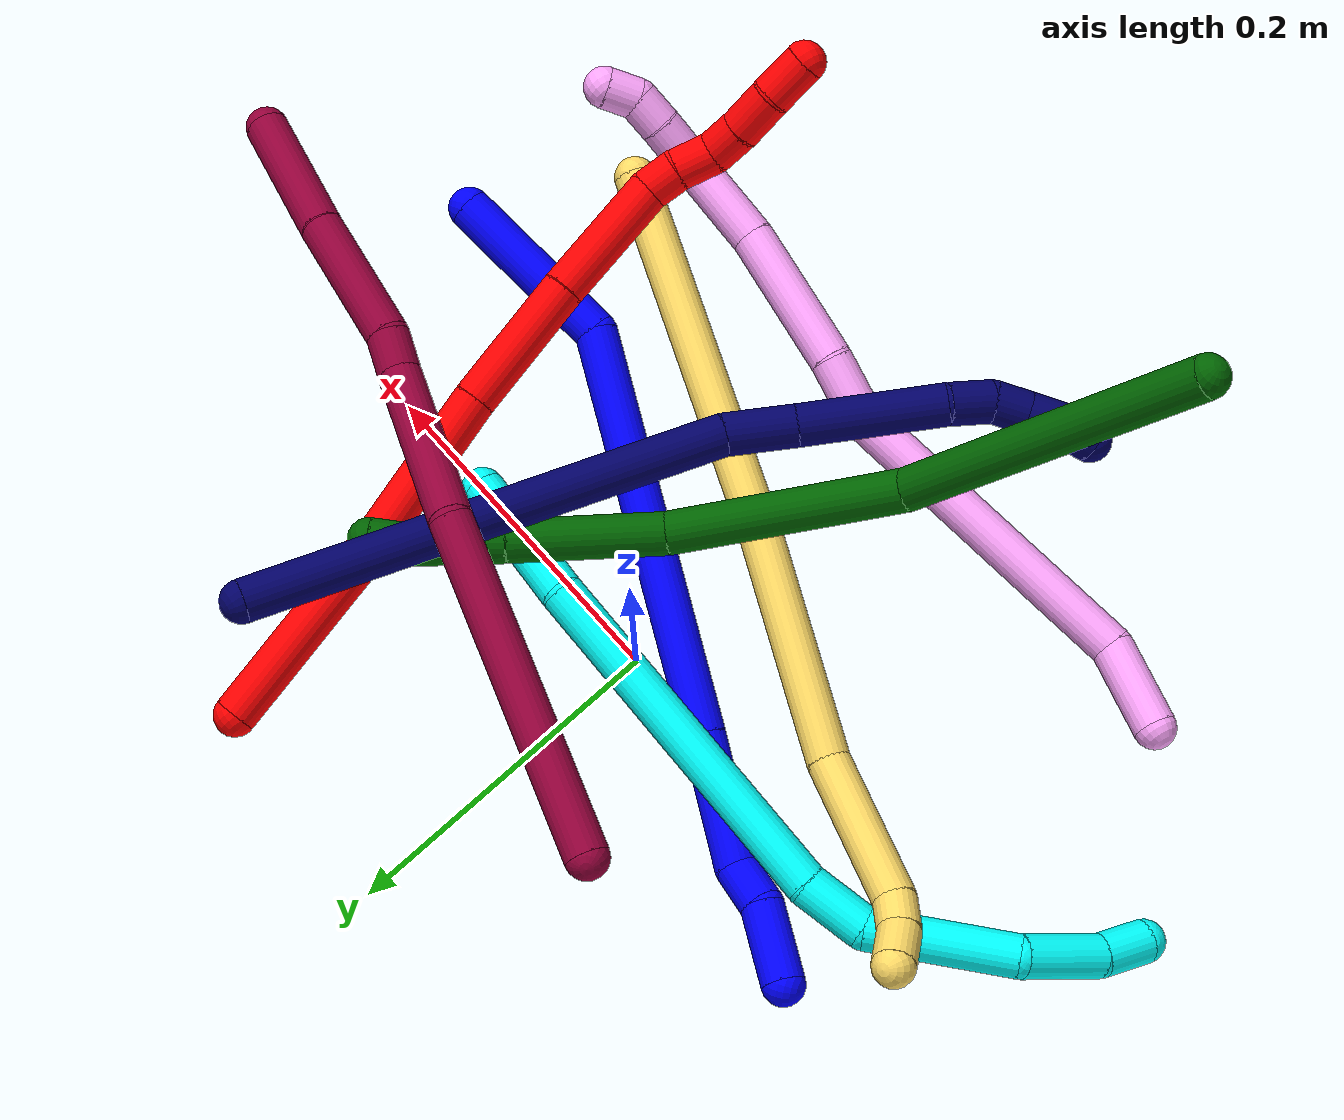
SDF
<sdf version="1.7">
 <world name="default">
  <plugin name="TubeGeneratorPlugin" filename="libtube_generator_plugin.so"/>
  <model name="photoneo_s_sensor">
   <static>1</static>
   <pose>0 0 2 1.57079 1.57079 3.14159</pose>
   <link name="link">
    <inertial><mass>0.1</mass></inertial>
    <sensor name="sensor" type="depth">
     <update_rate>30</update_rate>
     <camera>
      <horizontal_fov>1.22</horizontal_fov>
      <image><width>1920</width><height>1200</height><format>B8G8R8</format></image>
      <clip><near>0.1</near><far>4</far></clip>
      <depth_camera><output>points</output></depth_camera>
     </camera>
     <plugin name="camera_plugin" filename="libgazebo_ros_depth_camera.so">
      <baseline>0.2</baseline>
      <alwaysOn>1</alwaysOn>
      <updateRate>0.0</updateRate>
      <cameraName>camera_ir</cameraName>
      <imageTopicName>/camera/color/image_raw</imageTopicName>
      <cameraInfoTopicName>/camera/color/camera_info</cameraInfoTopicName>
      <depthImageTopicName>/camera/depth/image_raw</depthImageTopicName>
      <depthImageCameraInfoTopicName>/camera/depth/camera_info</depthImageCameraInfoTopicName>
      <pointCloudTopicName>/camera/depth/points</pointCloudTopicName>
      <frameName>fr_optical</frameName>
      <pointCloudCutoff>0.1</pointCloudCutoff>
      <pointCloudCutoffMax>2.0</pointCloudCutoffMax>
      <distortionK1>0</distortionK1>
      <distortionK2>0</distortionK2>
      <distortionK3>0</distortionK3>
      <distortionT1>0</distortionT1>
      <distortionT2>0</distortionT2>
      <CxPrime>0</CxPrime>
      <Cx>0</Cx>
      <Cy>0</Cy>
      <focalLength>0</focalLength>
      <hackBaseline>0</hackBaseline>
     </plugin>
    </sensor>
   </link>
  </model>
  <gravity>0 0 -9.8</gravity>
  <magnetic_field>6e-06 2.3e-05 -4.2e-05</magnetic_field>
  <atmosphere type="adiabatic"/>
  <physics name="default_physics" default="0" type="ode">
   <max_step_size>0.003</max_step_size>
   <real_time_factor>1</real_time_factor>
   <real_time_update_rate>1000</real_time_update_rate>
   <max_contacts>10000</max_contacts>
   <ode>
    <solver>
     <type>quick</type>
     <iters>100</iters>
     <sor>1.3</sor>
     <use_dynamic_moi_rescaling>0</use_dynamic_moi_rescaling>
    </solver>
    <constraints>
     <contact_max_correcting_vel>0</contact_max_correcting_vel>
     <contact_surface_layer>0.001</contact_surface_layer>
     <cfm>0</cfm>
     <erp>0.2</erp>
    </constraints>
   </ode>
  </physics>
  <scene><ambient>0.4 0.4 0.4 1</ambient><background>0.7 0.7 0.7 1</background><shadows>0</shadows></scene>
  <audio><device>default</device></audio>
  <spherical_coordinates>
   <surface_model>EARTH_WGS84</surface_model>
   <latitude_deg>0</latitude_deg>
   <longitude_deg>0</longitude_deg>
   <elevation>0</elevation>
   <heading_deg>0</heading_deg>
  </spherical_coordinates>
  <model name="bin">
   <static>1</static>
   <link name="bottom">
    <collision name="collision-bottom">
     <pose>0 0 -0.01 0 -0 0</pose>
     <geometry><box><size>0.8 0.6 0.02</size></box></geometry>
     <surface>
      <friction><ode><mu>100</mu><mu2>100</mu2></ode></friction>
      <contact><collide_bitmask>65535</collide_bitmask></contact>
     </surface>
    </collision>
   </link>
   <link name="west_wall">
    <collision name="collision-west_wall">
     <pose>-0.41 0 0.1 0 -0 0</pose>
     <geometry><box><size>0.02 0.6 0.2</size></box></geometry>
     <surface>
      <friction><ode><mu>100</mu><mu2>100</mu2></ode></friction>
      <contact><collide_bitmask>65535</collide_bitmask></contact>
     </surface>
    </collision>
   </link>
   <link name="east_wall">
    <collision name="collision-east_wall">
     <pose>0.41 0 0.1 0 -0 0</pose>
     <geometry><box><size>0.02 0.6 0.2</size></box></geometry>
     <surface>
      <friction><ode><mu>100</mu><mu2>100</mu2></ode></friction>
      <contact><collide_bitmask>65535</collide_bitmask></contact>
     </surface>
    </collision>
   </link>
   <link name="south_wall">
    <collision name="collision-south_wall">
     <pose>0 -0.31 0.1 0 -0 0</pose>
     <geometry><box><size>0.8 0.02 0.2</size></box></geometry>
     <surface>
      <friction><ode><mu>100</mu><mu2>100</mu2></ode></friction>
      <contact><collide_bitmask>65535</collide_bitmask></contact>
     </surface>
    </collision>
   </link>
   <link name="north_wall">
    <collision name="collision-north_wall">
     <pose>0 0.31 0.1 0 -0 0</pose>
     <geometry><box><size>0.8 0.02 0.2</size></box></geometry>
     <surface>
      <friction><ode><mu>100</mu><mu2>100</mu2></ode></friction>
      <contact><collide_bitmask>65535</collide_bitmask></contact>
     </surface>
    </collision>
   </link>
  </model>
  <model name="1">
   <static>0</static>
   <link name="1">
    <collision name="collision-cylinder-e_1_1_4">
     <pose>-0.022362 0.013182 -0.046416 -2.86489 -0.433988 2.01496</pose>
     <geometry><cylinder><radius>0.0125</radius><length>0.106363</length></cylinder></geometry>
     <surface>
      <friction><ode><mu>1.16</mu><mu2>1.16</mu2><slip1>0</slip1><slip2>0</slip2></ode></friction>
      <contact><ode><kp>1e+06</kp><kd>1</kd><max_vel>0</max_vel><min_depth>0.001</min_depth></ode></contact>
     </surface>
    </collision>
    <visual name="visual-cylinder-e_1_1_4">
     <pose>-0.022362 0.013182 -0.046416 -2.86489 -0.433988 2.01496</pose>
     <geometry><cylinder><radius>0.0125</radius><length>0.106363</length></cylinder></geometry>
     <material><ambient>0 0 1 1</ambient></material>
    </visual>
    <collision name="collision-cylinder-e_2_4_5">
     <pose>-0.142154 0.058589 -0.157604 -2.67992 -0.932076 2.26738</pose>
     <geometry><cylinder><radius>0.0125</radius><length>0.242704</length></cylinder></geometry>
     <surface>
      <friction><ode><mu>1.16</mu><mu2>1.16</mu2><slip1>0</slip1><slip2>0</slip2></ode></friction>
      <contact><ode><kp>1e+06</kp><kd>1</kd><max_vel>0</max_vel><min_depth>0.001</min_depth></ode></contact>
     </surface>
    </collision>
    <visual name="visual-cylinder-e_2_4_5">
     <pose>-0.142154 0.058589 -0.157604 -2.67992 -0.932076 2.26738</pose>
     <geometry><cylinder><radius>0.0125</radius><length>0.242704</length></cylinder></geometry>
     <material><ambient>0 0 1 1</ambient></material>
    </visual>
    <collision name="collision-cylinder-e_3_5_6">
     <pose>-0.270903 0.100968 -0.242415 -2.67261 -0.948621 2.27059</pose>
     <geometry><cylinder><radius>0.0125</radius><length>0.077088</length></cylinder></geometry>
     <surface>
      <friction><ode><mu>1.16</mu><mu2>1.16</mu2><slip1>0</slip1><slip2>0</slip2></ode></friction>
      <contact><ode><kp>1e+06</kp><kd>1</kd><max_vel>0</max_vel><min_depth>0.001</min_depth></ode></contact>
     </surface>
    </collision>
    <visual name="visual-cylinder-e_3_5_6">
     <pose>-0.270903 0.100968 -0.242415 -2.67261 -0.948621 2.27059</pose>
     <geometry><cylinder><radius>0.0125</radius><length>0.077088</length></cylinder></geometry>
     <material><ambient>0 0 1 1</ambient></material>
    </visual>
    <collision name="collision-cylinder-e_4_6_7">
     <pose>-0.310714 0.109721 -0.273283 3.01303 -0.660829 -2.77057</pose>
     <geometry><cylinder><radius>0.0125</radius><length>0.027664</length></cylinder></geometry>
     <surface>
      <friction><ode><mu>1.16</mu><mu2>1.16</mu2><slip1>0</slip1><slip2>0</slip2></ode></friction>
      <contact><ode><kp>1e+06</kp><kd>1</kd><max_vel>0</max_vel><min_depth>0.001</min_depth></ode></contact>
     </surface>
    </collision>
    <visual name="visual-cylinder-e_4_6_7">
     <pose>-0.310714 0.109721 -0.273283 3.01303 -0.660829 -2.77057</pose>
     <geometry><cylinder><radius>0.0125</radius><length>0.027664</length></cylinder></geometry>
     <material><ambient>0 0 1 1</ambient></material>
    </visual>
    <collision name="collision-cylinder-e_5_7_2">
     <pose>-0.338248 0.110109 -0.297048 -3.00424 -0.969758 2.88194</pose>
     <geometry><cylinder><radius>0.0125</radius><length>0.046182</length></cylinder></geometry>
     <surface>
      <friction><ode><mu>1.16</mu><mu2>1.16</mu2><slip1>0</slip1><slip2>0</slip2></ode></friction>
      <contact><ode><kp>1e+06</kp><kd>1</kd><max_vel>0</max_vel><min_depth>0.001</min_depth></ode></contact>
     </surface>
    </collision>
    <visual name="visual-cylinder-e_5_7_2">
     <pose>-0.338248 0.110109 -0.297048 -3.00424 -0.969758 2.88194</pose>
     <geometry><cylinder><radius>0.0125</radius><length>0.046182</length></cylinder></geometry>
     <material><ambient>0 0 1 1</ambient></material>
    </visual>
    <collision name="collision-sphere-2">
     <pose>-0.357292 0.111897 -0.309982 0 -0 0</pose>
     <geometry><sphere><radius>0.0125</radius></sphere></geometry>
     <surface>
      <friction><ode><mu>1.16</mu><mu2>1.16</mu2><slip1>0</slip1><slip2>0</slip2></ode></friction>
      <contact><ode><kp>1e+06</kp><kd>1</kd><max_vel>0</max_vel><min_depth>0.001</min_depth></ode></contact>
     </surface>
    </collision>
    <visual name="visual-sphere-2">
     <pose>-0.357292 0.111897 -0.309982 0 -0 0</pose>
     <geometry><sphere><radius>0.0125</radius></sphere></geometry>
     <material><ambient>0 0 1 1</ambient></material>
    </visual>
    <collision name="collision-sphere-7">
     <pose>-0.319204 0.108321 -0.284113 0 -0 0</pose>
     <geometry><sphere><radius>0.0125</radius></sphere></geometry>
     <surface>
      <friction><ode><mu>1.16</mu><mu2>1.16</mu2><slip1>0</slip1><slip2>0</slip2></ode></friction>
      <contact><ode><kp>1e+06</kp><kd>1</kd><max_vel>0</max_vel><min_depth>0.001</min_depth></ode></contact>
     </surface>
    </collision>
    <visual name="visual-sphere-7">
     <pose>-0.319204 0.108321 -0.284113 0 -0 0</pose>
     <geometry><sphere><radius>0.0125</radius></sphere></geometry>
     <material><ambient>0 0 1 1</ambient></material>
    </visual>
    <collision name="collision-sphere-6">
     <pose>-0.302225 0.111121 -0.262453 0 -0 0</pose>
     <geometry><sphere><radius>0.0125</radius></sphere></geometry>
     <surface>
      <friction><ode><mu>1.16</mu><mu2>1.16</mu2><slip1>0</slip1><slip2>0</slip2></ode></friction>
      <contact><ode><kp>1e+06</kp><kd>1</kd><max_vel>0</max_vel><min_depth>0.001</min_depth></ode></contact>
     </surface>
    </collision>
    <visual name="visual-sphere-6">
     <pose>-0.302225 0.111121 -0.262453 0 -0 0</pose>
     <geometry><sphere><radius>0.0125</radius></sphere></geometry>
     <material><ambient>0 0 1 1</ambient></material>
    </visual>
    <collision name="collision-sphere-5">
     <pose>-0.239582 0.090815 -0.222377 0 -0 0</pose>
     <geometry><sphere><radius>0.0125</radius></sphere></geometry>
     <surface>
      <friction><ode><mu>1.16</mu><mu2>1.16</mu2><slip1>0</slip1><slip2>0</slip2></ode></friction>
      <contact><ode><kp>1e+06</kp><kd>1</kd><max_vel>0</max_vel><min_depth>0.001</min_depth></ode></contact>
     </surface>
    </collision>
    <visual name="visual-sphere-5">
     <pose>-0.239582 0.090815 -0.222377 0 -0 0</pose>
     <geometry><sphere><radius>0.0125</radius></sphere></geometry>
     <material><ambient>0 0 1 1</ambient></material>
    </visual>
    <collision name="collision-sphere-1">
     <geometry><sphere><radius>0.0125</radius></sphere></geometry>
     <surface>
      <friction><ode><mu>1.16</mu><mu2>1.16</mu2><slip1>0</slip1><slip2>0</slip2></ode></friction>
      <contact><ode><kp>1e+06</kp><kd>1</kd><max_vel>0</max_vel><min_depth>0.001</min_depth></ode></contact>
     </surface>
    </collision>
    <visual name="visual-sphere-1">
     <geometry><sphere><radius>0.0125</radius></sphere></geometry>
     <material><ambient>0 0 1 1</ambient></material>
    </visual>
    <collision name="collision-sphere-4">
     <pose>-0.044725 0.026363 -0.092832 0 -0 0</pose>
     <geometry><sphere><radius>0.0125</radius></sphere></geometry>
     <surface>
      <friction><ode><mu>1.16</mu><mu2>1.16</mu2><slip1>0</slip1><slip2>0</slip2></ode></friction>
      <contact><ode><kp>1e+06</kp><kd>1</kd><max_vel>0</max_vel><min_depth>0.001</min_depth></ode></contact>
     </surface>
    </collision>
    <visual name="visual-sphere-4">
     <pose>-0.044725 0.026363 -0.092832 0 -0 0</pose>
     <geometry><sphere><radius>0.0125</radius></sphere></geometry>
     <material><ambient>0 0 1 1</ambient></material>
    </visual>
    <inertial>
     <pose>-0.163959 0.063051 -0.166307 0 -0 0</pose>
     <mass>0.5</mass>
     <inertia>
      <ixx>0.000103</ixx>
      <ixy>0</ixy>
      <ixz>0</ixz>
      <iyy>0.001783</iyy>
      <iyz>0</iyz>
      <izz>0.000671</izz>
     </inertia>
    </inertial>
   </link>
   <pose>0.264453 -0.103057 0.012493 -1.79643 0.159171 -1.08568</pose>
  </model>
  <model name="2">
   <static>0</static>
   <link name="2">
    <collision name="collision-cylinder-e_1_1_4">
     <pose>0.000698 -0.058525 -0.019623 1.89431 0.011301 0.015709</pose>
     <geometry><cylinder><radius>0.0125</radius><length>0.123461</length></cylinder></geometry>
     <surface>
      <friction><ode><mu>1.16</mu><mu2>1.16</mu2><slip1>0</slip1><slip2>0</slip2></ode></friction>
      <contact><ode><kp>1e+06</kp><kd>1</kd><max_vel>0</max_vel><min_depth>0.001</min_depth></ode></contact>
     </surface>
    </collision>
    <visual name="visual-cylinder-e_1_1_4">
     <pose>0.000698 -0.058525 -0.019623 1.89431 0.011301 0.015709</pose>
     <geometry><cylinder><radius>0.0125</radius><length>0.123461</length></cylinder></geometry>
     <material><ambient>1 0 0 1</ambient></material>
    </visual>
    <collision name="collision-cylinder-e_2_4_5">
     <pose>0.002526 -0.163512 -0.058023 1.95486 0.022559 0.033446</pose>
     <geometry><cylinder><radius>0.0125</radius><length>0.100253</length></cylinder></geometry>
     <surface>
      <friction><ode><mu>1.16</mu><mu2>1.16</mu2><slip1>0</slip1><slip2>0</slip2></ode></friction>
      <contact><ode><kp>1e+06</kp><kd>1</kd><max_vel>0</max_vel><min_depth>0.001</min_depth></ode></contact>
     </surface>
    </collision>
    <visual name="visual-cylinder-e_2_4_5">
     <pose>0.002526 -0.163512 -0.058023 1.95486 0.022559 0.033446</pose>
     <geometry><cylinder><radius>0.0125</radius><length>0.100253</length></cylinder></geometry>
     <material><ambient>1 0 0 1</ambient></material>
    </visual>
    <collision name="collision-cylinder-e_3_5_6">
     <pose>0.004439 -0.248471 -0.089668 1.89338 0.019264 0.026751</pose>
     <geometry><cylinder><radius>0.0125</radius><length>0.081194</length></cylinder></geometry>
     <surface>
      <friction><ode><mu>1.16</mu><mu2>1.16</mu2><slip1>0</slip1><slip2>0</slip2></ode></friction>
      <contact><ode><kp>1e+06</kp><kd>1</kd><max_vel>0</max_vel><min_depth>0.001</min_depth></ode></contact>
     </surface>
    </collision>
    <visual name="visual-cylinder-e_3_5_6">
     <pose>0.004439 -0.248471 -0.089668 1.89338 0.019264 0.026751</pose>
     <geometry><cylinder><radius>0.0125</radius><length>0.081194</length></cylinder></geometry>
     <material><ambient>1 0 0 1</ambient></material>
    </visual>
    <collision name="collision-cylinder-e_4_6_7">
     <pose>0.00422 -0.323212 -0.113584 1.86669 -0.026402 -0.035647</pose>
     <geometry><cylinder><radius>0.0125</radius><length>0.07581</length></cylinder></geometry>
     <surface>
      <friction><ode><mu>1.16</mu><mu2>1.16</mu2><slip1>0</slip1><slip2>0</slip2></ode></friction>
      <contact><ode><kp>1e+06</kp><kd>1</kd><max_vel>0</max_vel><min_depth>0.001</min_depth></ode></contact>
     </surface>
    </collision>
    <visual name="visual-cylinder-e_4_6_7">
     <pose>0.00422 -0.323212 -0.113584 1.86669 -0.026402 -0.035647</pose>
     <geometry><cylinder><radius>0.0125</radius><length>0.07581</length></cylinder></geometry>
     <material><ambient>1 0 0 1</ambient></material>
    </visual>
    <collision name="collision-cylinder-e_5_7_8">
     <pose>0.00509 -0.369381 -0.124536 1.56101 0.18626 0.184456</pose>
     <geometry><cylinder><radius>0.0125</radius><length>0.020198</length></cylinder></geometry>
     <surface>
      <friction><ode><mu>1.16</mu><mu2>1.16</mu2><slip1>0</slip1><slip2>0</slip2></ode></friction>
      <contact><ode><kp>1e+06</kp><kd>1</kd><max_vel>0</max_vel><min_depth>0.001</min_depth></ode></contact>
     </surface>
    </collision>
    <visual name="visual-cylinder-e_5_7_8">
     <pose>0.00509 -0.369381 -0.124536 1.56101 0.18626 0.184456</pose>
     <geometry><cylinder><radius>0.0125</radius><length>0.020198</length></cylinder></geometry>
     <material><ambient>1 0 0 1</ambient></material>
    </visual>
    <collision name="collision-cylinder-e_6_8_9">
     <pose>0.007862 -0.390847 -0.122476 1.40233 0.076891 0.064927</pose>
     <geometry><cylinder><radius>0.0125</radius><length>0.023484</length></cylinder></geometry>
     <surface>
      <friction><ode><mu>1.16</mu><mu2>1.16</mu2><slip1>0</slip1><slip2>0</slip2></ode></friction>
      <contact><ode><kp>1e+06</kp><kd>1</kd><max_vel>0</max_vel><min_depth>0.001</min_depth></ode></contact>
     </surface>
    </collision>
    <visual name="visual-cylinder-e_6_8_9">
     <pose>0.007862 -0.390847 -0.122476 1.40233 0.076891 0.064927</pose>
     <geometry><cylinder><radius>0.0125</radius><length>0.023484</length></cylinder></geometry>
     <material><ambient>1 0 0 1</ambient></material>
    </visual>
    <collision name="collision-cylinder-e_7_9_10">
     <pose>0.013982 -0.411724 -0.120355 1.55391 0.509667 0.501486</pose>
     <geometry><cylinder><radius>0.0125</radius><length>0.021393</length></cylinder></geometry>
     <surface>
      <friction><ode><mu>1.16</mu><mu2>1.16</mu2><slip1>0</slip1><slip2>0</slip2></ode></friction>
      <contact><ode><kp>1e+06</kp><kd>1</kd><max_vel>0</max_vel><min_depth>0.001</min_depth></ode></contact>
     </surface>
    </collision>
    <visual name="visual-cylinder-e_7_9_10">
     <pose>0.013982 -0.411724 -0.120355 1.55391 0.509667 0.501486</pose>
     <geometry><cylinder><radius>0.0125</radius><length>0.021393</length></cylinder></geometry>
     <material><ambient>1 0 0 1</ambient></material>
    </visual>
    <collision name="collision-cylinder-e_8_10_11">
     <pose>0.025794 -0.432784 -0.1213 1.6646 0.510369 0.558175</pose>
     <geometry><cylinder><radius>0.0125</radius><length>0.026991</length></cylinder></geometry>
     <surface>
      <friction><ode><mu>1.16</mu><mu2>1.16</mu2><slip1>0</slip1><slip2>0</slip2></ode></friction>
      <contact><ode><kp>1e+06</kp><kd>1</kd><max_vel>0</max_vel><min_depth>0.001</min_depth></ode></contact>
     </surface>
    </collision>
    <visual name="visual-cylinder-e_8_10_11">
     <pose>0.025794 -0.432784 -0.1213 1.6646 0.510369 0.558175</pose>
     <geometry><cylinder><radius>0.0125</radius><length>0.026991</length></cylinder></geometry>
     <material><ambient>1 0 0 1</ambient></material>
    </visual>
    <collision name="collision-cylinder-e_9_11_2">
     <pose>0.036899 -0.457243 -0.124016 1.69675 0.338035 0.382498</pose>
     <geometry><cylinder><radius>0.0125</radius><length>0.027215</length></cylinder></geometry>
     <surface>
      <friction><ode><mu>1.16</mu><mu2>1.16</mu2><slip1>0</slip1><slip2>0</slip2></ode></friction>
      <contact><ode><kp>1e+06</kp><kd>1</kd><max_vel>0</max_vel><min_depth>0.001</min_depth></ode></contact>
     </surface>
    </collision>
    <visual name="visual-cylinder-e_9_11_2">
     <pose>0.036899 -0.457243 -0.124016 1.69675 0.338035 0.382498</pose>
     <geometry><cylinder><radius>0.0125</radius><length>0.027215</length></cylinder></geometry>
     <material><ambient>1 0 0 1</ambient></material>
    </visual>
    <collision name="collision-sphere-2">
     <pose>0.041412 -0.469979 -0.125629 0 -0 0</pose>
     <geometry><sphere><radius>0.0125</radius></sphere></geometry>
     <surface>
      <friction><ode><mu>1.16</mu><mu2>1.16</mu2><slip1>0</slip1><slip2>0</slip2></ode></friction>
      <contact><ode><kp>1e+06</kp><kd>1</kd><max_vel>0</max_vel><min_depth>0.001</min_depth></ode></contact>
     </surface>
    </collision>
    <visual name="visual-sphere-2">
     <pose>0.041412 -0.469979 -0.125629 0 -0 0</pose>
     <geometry><sphere><radius>0.0125</radius></sphere></geometry>
     <material><ambient>1 0 0 1</ambient></material>
    </visual>
    <collision name="collision-sphere-11">
     <pose>0.032386 -0.444508 -0.122403 0 -0 0</pose>
     <geometry><sphere><radius>0.0125</radius></sphere></geometry>
     <surface>
      <friction><ode><mu>1.16</mu><mu2>1.16</mu2><slip1>0</slip1><slip2>0</slip2></ode></friction>
      <contact><ode><kp>1e+06</kp><kd>1</kd><max_vel>0</max_vel><min_depth>0.001</min_depth></ode></contact>
     </surface>
    </collision>
    <visual name="visual-sphere-11">
     <pose>0.032386 -0.444508 -0.122403 0 -0 0</pose>
     <geometry><sphere><radius>0.0125</radius></sphere></geometry>
     <material><ambient>1 0 0 1</ambient></material>
    </visual>
    <collision name="collision-sphere-10">
     <pose>0.019201 -0.42106 -0.120197 0 -0 0</pose>
     <geometry><sphere><radius>0.0125</radius></sphere></geometry>
     <surface>
      <friction><ode><mu>1.16</mu><mu2>1.16</mu2><slip1>0</slip1><slip2>0</slip2></ode></friction>
      <contact><ode><kp>1e+06</kp><kd>1</kd><max_vel>0</max_vel><min_depth>0.001</min_depth></ode></contact>
     </surface>
    </collision>
    <visual name="visual-sphere-10">
     <pose>0.019201 -0.42106 -0.120197 0 -0 0</pose>
     <geometry><sphere><radius>0.0125</radius></sphere></geometry>
     <material><ambient>1 0 0 1</ambient></material>
    </visual>
    <collision name="collision-sphere-9">
     <pose>0.008764 -0.402389 -0.120513 0 -0 0</pose>
     <geometry><sphere><radius>0.0125</radius></sphere></geometry>
     <surface>
      <friction><ode><mu>1.16</mu><mu2>1.16</mu2><slip1>0</slip1><slip2>0</slip2></ode></friction>
      <contact><ode><kp>1e+06</kp><kd>1</kd><max_vel>0</max_vel><min_depth>0.001</min_depth></ode></contact>
     </surface>
    </collision>
    <visual name="visual-sphere-9">
     <pose>0.008764 -0.402389 -0.120513 0 -0 0</pose>
     <geometry><sphere><radius>0.0125</radius></sphere></geometry>
     <material><ambient>1 0 0 1</ambient></material>
    </visual>
    <collision name="collision-sphere-4">
     <pose>0.001395 -0.117049 -0.039245 0 -0 0</pose>
     <geometry><sphere><radius>0.0125</radius></sphere></geometry>
     <surface>
      <friction><ode><mu>1.16</mu><mu2>1.16</mu2><slip1>0</slip1><slip2>0</slip2></ode></friction>
      <contact><ode><kp>1e+06</kp><kd>1</kd><max_vel>0</max_vel><min_depth>0.001</min_depth></ode></contact>
     </surface>
    </collision>
    <visual name="visual-sphere-4">
     <pose>0.001395 -0.117049 -0.039245 0 -0 0</pose>
     <geometry><sphere><radius>0.0125</radius></sphere></geometry>
     <material><ambient>1 0 0 1</ambient></material>
    </visual>
    <collision name="collision-sphere-1">
     <geometry><sphere><radius>0.0125</radius></sphere></geometry>
     <surface>
      <friction><ode><mu>1.16</mu><mu2>1.16</mu2><slip1>0</slip1><slip2>0</slip2></ode></friction>
      <contact><ode><kp>1e+06</kp><kd>1</kd><max_vel>0</max_vel><min_depth>0.001</min_depth></ode></contact>
     </surface>
    </collision>
    <visual name="visual-sphere-1">
     <geometry><sphere><radius>0.0125</radius></sphere></geometry>
     <material><ambient>1 0 0 1</ambient></material>
    </visual>
    <collision name="collision-sphere-8">
     <pose>0.00696 -0.379305 -0.124439 0 -0 0</pose>
     <geometry><sphere><radius>0.0125</radius></sphere></geometry>
     <surface>
      <friction><ode><mu>1.16</mu><mu2>1.16</mu2><slip1>0</slip1><slip2>0</slip2></ode></friction>
      <contact><ode><kp>1e+06</kp><kd>1</kd><max_vel>0</max_vel><min_depth>0.001</min_depth></ode></contact>
     </surface>
    </collision>
    <visual name="visual-sphere-8">
     <pose>0.00696 -0.379305 -0.124439 0 -0 0</pose>
     <geometry><sphere><radius>0.0125</radius></sphere></geometry>
     <material><ambient>1 0 0 1</ambient></material>
    </visual>
    <collision name="collision-sphere-5">
     <pose>0.003657 -0.209975 -0.0768 0 -0 0</pose>
     <geometry><sphere><radius>0.0125</radius></sphere></geometry>
     <surface>
      <friction><ode><mu>1.16</mu><mu2>1.16</mu2><slip1>0</slip1><slip2>0</slip2></ode></friction>
      <contact><ode><kp>1e+06</kp><kd>1</kd><max_vel>0</max_vel><min_depth>0.001</min_depth></ode></contact>
     </surface>
    </collision>
    <visual name="visual-sphere-5">
     <pose>0.003657 -0.209975 -0.0768 0 -0 0</pose>
     <geometry><sphere><radius>0.0125</radius></sphere></geometry>
     <material><ambient>1 0 0 1</ambient></material>
    </visual>
    <collision name="collision-sphere-6">
     <pose>0.005221 -0.286967 -0.102535 0 -0 0</pose>
     <geometry><sphere><radius>0.0125</radius></sphere></geometry>
     <surface>
      <friction><ode><mu>1.16</mu><mu2>1.16</mu2><slip1>0</slip1><slip2>0</slip2></ode></friction>
      <contact><ode><kp>1e+06</kp><kd>1</kd><max_vel>0</max_vel><min_depth>0.001</min_depth></ode></contact>
     </surface>
    </collision>
    <visual name="visual-sphere-6">
     <pose>0.005221 -0.286967 -0.102535 0 -0 0</pose>
     <geometry><sphere><radius>0.0125</radius></sphere></geometry>
     <material><ambient>1 0 0 1</ambient></material>
    </visual>
    <collision name="collision-sphere-7">
     <pose>0.003219 -0.359457 -0.124633 0 -0 0</pose>
     <geometry><sphere><radius>0.0125</radius></sphere></geometry>
     <surface>
      <friction><ode><mu>1.16</mu><mu2>1.16</mu2><slip1>0</slip1><slip2>0</slip2></ode></friction>
      <contact><ode><kp>1e+06</kp><kd>1</kd><max_vel>0</max_vel><min_depth>0.001</min_depth></ode></contact>
     </surface>
    </collision>
    <visual name="visual-sphere-7">
     <pose>0.003219 -0.359457 -0.124633 0 -0 0</pose>
     <geometry><sphere><radius>0.0125</radius></sphere></geometry>
     <material><ambient>1 0 0 1</ambient></material>
    </visual>
    <inertial>
     <pose>0.006613 -0.235736 -0.077493 0 -0 0</pose>
     <mass>0.5</mass>
     <inertia>
      <ixx>0.000357</ixx>
      <ixy>0</ixy>
      <ixz>0</ixz>
      <iyy>-0.000137</iyy>
      <iyz>0</iyz>
      <izz>0.00031</izz>
     </inertia>
    </inertial>
   </link>
   <pose>0.124942 0.19083 0.01243 -1.29265 -1.48587 1.14385</pose>
  </model>
  <model name="3">
   <static>0</static>
   <link name="3">
    <collision name="collision-cylinder-e_1_1_4">
     <pose>-0.035544 0.001654 0.020373 -0.08103 -1.04892 0.046893</pose>
     <geometry><cylinder><radius>0.0125</radius><length>0.082005</length></cylinder></geometry>
     <surface>
      <friction><ode><mu>1.16</mu><mu2>1.16</mu2><slip1>0</slip1><slip2>0</slip2></ode></friction>
      <contact><ode><kp>1e+06</kp><kd>1</kd><max_vel>0</max_vel><min_depth>0.001</min_depth></ode></contact>
     </surface>
    </collision>
    <visual name="visual-cylinder-e_1_1_4">
     <pose>-0.035544 0.001654 0.020373 -0.08103 -1.04892 0.046893</pose>
     <geometry><cylinder><radius>0.0125</radius><length>0.082005</length></cylinder></geometry>
     <material><ambient>0.003922 1 0.996078 1</ambient></material>
    </visual>
    <collision name="collision-cylinder-e_2_4_5">
     <pose>-0.171732 -0.005191 0.075095 0.242589 -1.23271 -0.172275</pose>
     <geometry><cylinder><radius>0.0125</radius><length>0.213364</length></cylinder></geometry>
     <surface>
      <friction><ode><mu>1.16</mu><mu2>1.16</mu2><slip1>0</slip1><slip2>0</slip2></ode></friction>
      <contact><ode><kp>1e+06</kp><kd>1</kd><max_vel>0</max_vel><min_depth>0.001</min_depth></ode></contact>
     </surface>
    </collision>
    <visual name="visual-cylinder-e_2_4_5">
     <pose>-0.171732 -0.005191 0.075095 0.242589 -1.23271 -0.172275</pose>
     <geometry><cylinder><radius>0.0125</radius><length>0.213364</length></cylinder></geometry>
     <material><ambient>0.003922 1 0.996078 1</ambient></material>
    </visual>
    <collision name="collision-cylinder-e_3_5_6">
     <pose>-0.289789 -0.019485 0.116359 0.697386 -1.09279 -0.43519</pose>
     <geometry><cylinder><radius>0.0125</radius><length>0.039225</length></cylinder></geometry>
     <surface>
      <friction><ode><mu>1.16</mu><mu2>1.16</mu2><slip1>0</slip1><slip2>0</slip2></ode></friction>
      <contact><ode><kp>1e+06</kp><kd>1</kd><max_vel>0</max_vel><min_depth>0.001</min_depth></ode></contact>
     </surface>
    </collision>
    <visual name="visual-cylinder-e_3_5_6">
     <pose>-0.289789 -0.019485 0.116359 0.697386 -1.09279 -0.43519</pose>
     <geometry><cylinder><radius>0.0125</radius><length>0.039225</length></cylinder></geometry>
     <material><ambient>0.003922 1 0.996078 1</ambient></material>
    </visual>
    <collision name="collision-cylinder-e_4_6_7">
     <pose>-0.33348 -0.053903 0.141582 1.00178 -0.658301 -0.369726</pose>
     <geometry><cylinder><radius>0.0125</radius><length>0.085906</length></cylinder></geometry>
     <surface>
      <friction><ode><mu>1.16</mu><mu2>1.16</mu2><slip1>0</slip1><slip2>0</slip2></ode></friction>
      <contact><ode><kp>1e+06</kp><kd>1</kd><max_vel>0</max_vel><min_depth>0.001</min_depth></ode></contact>
     </surface>
    </collision>
    <visual name="visual-cylinder-e_4_6_7">
     <pose>-0.33348 -0.053903 0.141582 1.00178 -0.658301 -0.369726</pose>
     <geometry><cylinder><radius>0.0125</radius><length>0.085906</length></cylinder></geometry>
     <material><ambient>0.003922 1 0.996078 1</ambient></material>
    </visual>
    <collision name="collision-cylinder-e_5_7_8">
     <pose>-0.372505 -0.103727 0.158859 1.61933 -0.540809 -0.56633</pose>
     <geometry><cylinder><radius>0.0125</radius><length>0.049518</length></cylinder></geometry>
     <surface>
      <friction><ode><mu>1.16</mu><mu2>1.16</mu2><slip1>0</slip1><slip2>0</slip2></ode></friction>
      <contact><ode><kp>1e+06</kp><kd>1</kd><max_vel>0</max_vel><min_depth>0.001</min_depth></ode></contact>
     </surface>
    </collision>
    <visual name="visual-cylinder-e_5_7_8">
     <pose>-0.372505 -0.103727 0.158859 1.61933 -0.540809 -0.56633</pose>
     <geometry><cylinder><radius>0.0125</radius><length>0.049518</length></cylinder></geometry>
     <material><ambient>0.003922 1 0.996078 1</ambient></material>
    </visual>
    <collision name="collision-cylinder-e_6_8_2">
     <pose>-0.389347 -0.13931 0.156781 1.64357 -0.276706 -0.297318</pose>
     <geometry><cylinder><radius>0.0125</radius><length>0.029982</length></cylinder></geometry>
     <surface>
      <friction><ode><mu>1.16</mu><mu2>1.16</mu2><slip1>0</slip1><slip2>0</slip2></ode></friction>
      <contact><ode><kp>1e+06</kp><kd>1</kd><max_vel>0</max_vel><min_depth>0.001</min_depth></ode></contact>
     </surface>
    </collision>
    <visual name="visual-cylinder-e_6_8_2">
     <pose>-0.389347 -0.13931 0.156781 1.64357 -0.276706 -0.297318</pose>
     <geometry><cylinder><radius>0.0125</radius><length>0.029982</length></cylinder></geometry>
     <material><ambient>0.003922 1 0.996078 1</ambient></material>
    </visual>
    <collision name="collision-sphere-2">
     <pose>-0.393442 -0.153692 0.155732 0 -0 0</pose>
     <geometry><sphere><radius>0.0125</radius></sphere></geometry>
     <surface>
      <friction><ode><mu>1.16</mu><mu2>1.16</mu2><slip1>0</slip1><slip2>0</slip2></ode></friction>
      <contact><ode><kp>1e+06</kp><kd>1</kd><max_vel>0</max_vel><min_depth>0.001</min_depth></ode></contact>
     </surface>
    </collision>
    <visual name="visual-sphere-2">
     <pose>-0.393442 -0.153692 0.155732 0 -0 0</pose>
     <geometry><sphere><radius>0.0125</radius></sphere></geometry>
     <material><ambient>0.003922 1 0.996078 1</ambient></material>
    </visual>
    <collision name="collision-sphere-4">
     <pose>-0.071089 0.003309 0.040746 0 -0 0</pose>
     <geometry><sphere><radius>0.0125</radius></sphere></geometry>
     <surface>
      <friction><ode><mu>1.16</mu><mu2>1.16</mu2><slip1>0</slip1><slip2>0</slip2></ode></friction>
      <contact><ode><kp>1e+06</kp><kd>1</kd><max_vel>0</max_vel><min_depth>0.001</min_depth></ode></contact>
     </surface>
    </collision>
    <visual name="visual-sphere-4">
     <pose>-0.071089 0.003309 0.040746 0 -0 0</pose>
     <geometry><sphere><radius>0.0125</radius></sphere></geometry>
     <material><ambient>0.003922 1 0.996078 1</ambient></material>
    </visual>
    <collision name="collision-sphere-1">
     <geometry><sphere><radius>0.0125</radius></sphere></geometry>
     <surface>
      <friction><ode><mu>1.16</mu><mu2>1.16</mu2><slip1>0</slip1><slip2>0</slip2></ode></friction>
      <contact><ode><kp>1e+06</kp><kd>1</kd><max_vel>0</max_vel><min_depth>0.001</min_depth></ode></contact>
     </surface>
    </collision>
    <visual name="visual-sphere-1">
     <geometry><sphere><radius>0.0125</radius></sphere></geometry>
     <material><ambient>0.003922 1 0.996078 1</ambient></material>
    </visual>
    <collision name="collision-sphere-8">
     <pose>-0.385251 -0.124927 0.15783 0 -0 0</pose>
     <geometry><sphere><radius>0.0125</radius></sphere></geometry>
     <surface>
      <friction><ode><mu>1.16</mu><mu2>1.16</mu2><slip1>0</slip1><slip2>0</slip2></ode></friction>
      <contact><ode><kp>1e+06</kp><kd>1</kd><max_vel>0</max_vel><min_depth>0.001</min_depth></ode></contact>
     </surface>
    </collision>
    <visual name="visual-sphere-8">
     <pose>-0.385251 -0.124927 0.15783 0 -0 0</pose>
     <geometry><sphere><radius>0.0125</radius></sphere></geometry>
     <material><ambient>0.003922 1 0.996078 1</ambient></material>
    </visual>
    <collision name="collision-sphere-5">
     <pose>-0.272375 -0.013691 0.109444 0 -0 0</pose>
     <geometry><sphere><radius>0.0125</radius></sphere></geometry>
     <surface>
      <friction><ode><mu>1.16</mu><mu2>1.16</mu2><slip1>0</slip1><slip2>0</slip2></ode></friction>
      <contact><ode><kp>1e+06</kp><kd>1</kd><max_vel>0</max_vel><min_depth>0.001</min_depth></ode></contact>
     </surface>
    </collision>
    <visual name="visual-sphere-5">
     <pose>-0.272375 -0.013691 0.109444 0 -0 0</pose>
     <geometry><sphere><radius>0.0125</radius></sphere></geometry>
     <material><ambient>0.003922 1 0.996078 1</ambient></material>
    </visual>
    <collision name="collision-sphere-6">
     <pose>-0.307203 -0.025279 0.123275 0 -0 0</pose>
     <geometry><sphere><radius>0.0125</radius></sphere></geometry>
     <surface>
      <friction><ode><mu>1.16</mu><mu2>1.16</mu2><slip1>0</slip1><slip2>0</slip2></ode></friction>
      <contact><ode><kp>1e+06</kp><kd>1</kd><max_vel>0</max_vel><min_depth>0.001</min_depth></ode></contact>
     </surface>
    </collision>
    <visual name="visual-sphere-6">
     <pose>-0.307203 -0.025279 0.123275 0 -0 0</pose>
     <geometry><sphere><radius>0.0125</radius></sphere></geometry>
     <material><ambient>0.003922 1 0.996078 1</ambient></material>
    </visual>
    <collision name="collision-sphere-7">
     <pose>-0.359758 -0.082526 0.159889 0 -0 0</pose>
     <geometry><sphere><radius>0.0125</radius></sphere></geometry>
     <surface>
      <friction><ode><mu>1.16</mu><mu2>1.16</mu2><slip1>0</slip1><slip2>0</slip2></ode></friction>
      <contact><ode><kp>1e+06</kp><kd>1</kd><max_vel>0</max_vel><min_depth>0.001</min_depth></ode></contact>
     </surface>
    </collision>
    <visual name="visual-sphere-7">
     <pose>-0.359758 -0.082526 0.159889 0 -0 0</pose>
     <geometry><sphere><radius>0.0125</radius></sphere></geometry>
     <material><ambient>0.003922 1 0.996078 1</ambient></material>
    </visual>
    <inertial>
     <pose>-0.21938 -0.03136 0.093974 0 -0 0</pose>
     <mass>0.5</mass>
     <inertia>
      <ixx>0.000248</ixx>
      <ixy>0</ixy>
      <ixz>0</ixz>
      <iyy>0.000829</iyy>
      <iyz>0</iyz>
      <izz>0.00099</izz>
     </inertia>
    </inertial>
   </link>
   <pose>0.131466 0.001203 0.013249 0.270068 -0.273043 -0.198391</pose>
  </model>
  <model name="4">
   <static>0</static>
   <link name="4">
    <collision name="collision-cylinder-e_1_1_4">
     <pose>0.000594 0.002263 0.026253 -0.085987 0.022534 -0.000969</pose>
     <geometry><cylinder><radius>0.0125</radius><length>0.052714</length></cylinder></geometry>
     <surface>
      <friction><ode><mu>1.16</mu><mu2>1.16</mu2><slip1>0</slip1><slip2>0</slip2></ode></friction>
      <contact><ode><kp>1e+06</kp><kd>1</kd><max_vel>0</max_vel><min_depth>0.001</min_depth></ode></contact>
     </surface>
    </collision>
    <visual name="visual-cylinder-e_1_1_4">
     <pose>0.000594 0.002263 0.026253 -0.085987 0.022534 -0.000969</pose>
     <geometry><cylinder><radius>0.0125</radius><length>0.052714</length></cylinder></geometry>
     <material><ambient>1 0.65098 0.996078 1</ambient></material>
    </visual>
    <collision name="collision-cylinder-e_2_4_5">
     <pose>0.014272 -0.024214 0.143864 0.304784 0.135776 0.020884</pose>
     <geometry><cylinder><radius>0.0125</radius><length>0.193323</length></cylinder></geometry>
     <surface>
      <friction><ode><mu>1.16</mu><mu2>1.16</mu2><slip1>0</slip1><slip2>0</slip2></ode></friction>
      <contact><ode><kp>1e+06</kp><kd>1</kd><max_vel>0</max_vel><min_depth>0.001</min_depth></ode></contact>
     </surface>
    </collision>
    <visual name="visual-cylinder-e_2_4_5">
     <pose>0.014272 -0.024214 0.143864 0.304784 0.135776 0.020884</pose>
     <geometry><cylinder><radius>0.0125</radius><length>0.193323</length></cylinder></geometry>
     <material><ambient>1 0.65098 0.996078 1</ambient></material>
    </visual>
    <collision name="collision-cylinder-e_3_5_6">
     <pose>0.032724 -0.052778 0.253431 -0.009684 0.286677 -0.001398</pose>
     <geometry><cylinder><radius>0.0125</radius><length>0.037969</length></cylinder></geometry>
     <surface>
      <friction><ode><mu>1.16</mu><mu2>1.16</mu2><slip1>0</slip1><slip2>0</slip2></ode></friction>
      <contact><ode><kp>1e+06</kp><kd>1</kd><max_vel>0</max_vel><min_depth>0.001</min_depth></ode></contact>
     </surface>
    </collision>
    <visual name="visual-cylinder-e_3_5_6">
     <pose>0.032724 -0.052778 0.253431 -0.009684 0.286677 -0.001398</pose>
     <geometry><cylinder><radius>0.0125</radius><length>0.037969</length></cylinder></geometry>
     <material><ambient>1 0.65098 0.996078 1</ambient></material>
    </visual>
    <collision name="collision-cylinder-e_4_6_7">
     <pose>0.04321 -0.053935 0.315125 0.030655 0.117092 0.001797</pose>
     <geometry><cylinder><radius>0.0125</radius><length>0.08761</length></cylinder></geometry>
     <surface>
      <friction><ode><mu>1.16</mu><mu2>1.16</mu2><slip1>0</slip1><slip2>0</slip2></ode></friction>
      <contact><ode><kp>1e+06</kp><kd>1</kd><max_vel>0</max_vel><min_depth>0.001</min_depth></ode></contact>
     </surface>
    </collision>
    <visual name="visual-cylinder-e_4_6_7">
     <pose>0.04321 -0.053935 0.315125 0.030655 0.117092 0.001797</pose>
     <geometry><cylinder><radius>0.0125</radius><length>0.08761</length></cylinder></geometry>
     <material><ambient>1 0.65098 0.996078 1</ambient></material>
    </visual>
    <collision name="collision-cylinder-e_5_7_8">
     <pose>0.05296 -0.060476 0.390929 0.159757 0.140571 0.011271</pose>
     <geometry><cylinder><radius>0.0125</radius><length>0.066126</length></cylinder></geometry>
     <surface>
      <friction><ode><mu>1.16</mu><mu2>1.16</mu2><slip1>0</slip1><slip2>0</slip2></ode></friction>
      <contact><ode><kp>1e+06</kp><kd>1</kd><max_vel>0</max_vel><min_depth>0.001</min_depth></ode></contact>
     </surface>
    </collision>
    <visual name="visual-cylinder-e_5_7_8">
     <pose>0.05296 -0.060476 0.390929 0.159757 0.140571 0.011271</pose>
     <geometry><cylinder><radius>0.0125</radius><length>0.066126</length></cylinder></geometry>
     <material><ambient>1 0.65098 0.996078 1</ambient></material>
    </visual>
    <collision name="collision-cylinder-e_6_8_9">
     <pose>0.063799 -0.068554 0.431686 0.327988 0.608337 0.103798</pose>
     <geometry><cylinder><radius>0.0125</radius><length>0.02172</length></cylinder></geometry>
     <surface>
      <friction><ode><mu>1.16</mu><mu2>1.16</mu2><slip1>0</slip1><slip2>0</slip2></ode></friction>
      <contact><ode><kp>1e+06</kp><kd>1</kd><max_vel>0</max_vel><min_depth>0.001</min_depth></ode></contact>
     </surface>
    </collision>
    <visual name="visual-cylinder-e_6_8_9">
     <pose>0.063799 -0.068554 0.431686 0.327988 0.608337 0.103798</pose>
     <geometry><cylinder><radius>0.0125</radius><length>0.02172</length></cylinder></geometry>
     <material><ambient>1 0.65098 0.996078 1</ambient></material>
    </visual>
    <collision name="collision-cylinder-e_7_9_10">
     <pose>0.074913 -0.074265 0.448544 0.325218 0.504553 0.084527</pose>
     <geometry><cylinder><radius>0.0125</radius><length>0.020305</length></cylinder></geometry>
     <surface>
      <friction><ode><mu>1.16</mu><mu2>1.16</mu2><slip1>0</slip1><slip2>0</slip2></ode></friction>
      <contact><ode><kp>1e+06</kp><kd>1</kd><max_vel>0</max_vel><min_depth>0.001</min_depth></ode></contact>
     </surface>
    </collision>
    <visual name="visual-cylinder-e_7_9_10">
     <pose>0.074913 -0.074265 0.448544 0.325218 0.504553 0.084527</pose>
     <geometry><cylinder><radius>0.0125</radius><length>0.020305</length></cylinder></geometry>
     <material><ambient>1 0.65098 0.996078 1</ambient></material>
    </visual>
    <collision name="collision-cylinder-e_8_10_2">
     <pose>0.083243 -0.084331 0.463163 0.861881 0.345037 0.159885</pose>
     <geometry><cylinder><radius>0.0125</radius><length>0.020232</length></cylinder></geometry>
     <surface>
      <friction><ode><mu>1.16</mu><mu2>1.16</mu2><slip1>0</slip1><slip2>0</slip2></ode></friction>
      <contact><ode><kp>1e+06</kp><kd>1</kd><max_vel>0</max_vel><min_depth>0.001</min_depth></ode></contact>
     </surface>
    </collision>
    <visual name="visual-cylinder-e_8_10_2">
     <pose>0.083243 -0.084331 0.463163 0.861881 0.345037 0.159885</pose>
     <geometry><cylinder><radius>0.0125</radius><length>0.020232</length></cylinder></geometry>
     <material><ambient>1 0.65098 0.996078 1</ambient></material>
    </visual>
    <collision name="collision-sphere-2">
     <pose>0.086664 -0.091557 0.469361 0 -0 0</pose>
     <geometry><sphere><radius>0.0125</radius></sphere></geometry>
     <surface>
      <friction><ode><mu>1.16</mu><mu2>1.16</mu2><slip1>0</slip1><slip2>0</slip2></ode></friction>
      <contact><ode><kp>1e+06</kp><kd>1</kd><max_vel>0</max_vel><min_depth>0.001</min_depth></ode></contact>
     </surface>
    </collision>
    <visual name="visual-sphere-2">
     <pose>0.086664 -0.091557 0.469361 0 -0 0</pose>
     <geometry><sphere><radius>0.0125</radius></sphere></geometry>
     <material><ambient>1 0.65098 0.996078 1</ambient></material>
    </visual>
    <collision name="collision-sphere-10">
     <pose>0.079821 -0.077105 0.456966 0 -0 0</pose>
     <geometry><sphere><radius>0.0125</radius></sphere></geometry>
     <surface>
      <friction><ode><mu>1.16</mu><mu2>1.16</mu2><slip1>0</slip1><slip2>0</slip2></ode></friction>
      <contact><ode><kp>1e+06</kp><kd>1</kd><max_vel>0</max_vel><min_depth>0.001</min_depth></ode></contact>
     </surface>
    </collision>
    <visual name="visual-sphere-10">
     <pose>0.079821 -0.077105 0.456966 0 -0 0</pose>
     <geometry><sphere><radius>0.0125</radius></sphere></geometry>
     <material><ambient>1 0.65098 0.996078 1</ambient></material>
    </visual>
    <collision name="collision-sphere-9">
     <pose>0.070006 -0.071425 0.440123 0 -0 0</pose>
     <geometry><sphere><radius>0.0125</radius></sphere></geometry>
     <surface>
      <friction><ode><mu>1.16</mu><mu2>1.16</mu2><slip1>0</slip1><slip2>0</slip2></ode></friction>
      <contact><ode><kp>1e+06</kp><kd>1</kd><max_vel>0</max_vel><min_depth>0.001</min_depth></ode></contact>
     </surface>
    </collision>
    <visual name="visual-sphere-9">
     <pose>0.070006 -0.071425 0.440123 0 -0 0</pose>
     <geometry><sphere><radius>0.0125</radius></sphere></geometry>
     <material><ambient>1 0.65098 0.996078 1</ambient></material>
    </visual>
    <collision name="collision-sphere-4">
     <pose>0.001188 0.004526 0.052506 0 -0 0</pose>
     <geometry><sphere><radius>0.0125</radius></sphere></geometry>
     <surface>
      <friction><ode><mu>1.16</mu><mu2>1.16</mu2><slip1>0</slip1><slip2>0</slip2></ode></friction>
      <contact><ode><kp>1e+06</kp><kd>1</kd><max_vel>0</max_vel><min_depth>0.001</min_depth></ode></contact>
     </surface>
    </collision>
    <visual name="visual-sphere-4">
     <pose>0.001188 0.004526 0.052506 0 -0 0</pose>
     <geometry><sphere><radius>0.0125</radius></sphere></geometry>
     <material><ambient>1 0.65098 0.996078 1</ambient></material>
    </visual>
    <collision name="collision-sphere-1">
     <geometry><sphere><radius>0.0125</radius></sphere></geometry>
     <surface>
      <friction><ode><mu>1.16</mu><mu2>1.16</mu2><slip1>0</slip1><slip2>0</slip2></ode></friction>
      <contact><ode><kp>1e+06</kp><kd>1</kd><max_vel>0</max_vel><min_depth>0.001</min_depth></ode></contact>
     </surface>
    </collision>
    <visual name="visual-sphere-1">
     <geometry><sphere><radius>0.0125</radius></sphere></geometry>
     <material><ambient>1 0.65098 0.996078 1</ambient></material>
    </visual>
    <collision name="collision-sphere-8">
     <pose>0.057592 -0.065684 0.423249 0 -0 0</pose>
     <geometry><sphere><radius>0.0125</radius></sphere></geometry>
     <surface>
      <friction><ode><mu>1.16</mu><mu2>1.16</mu2><slip1>0</slip1><slip2>0</slip2></ode></friction>
      <contact><ode><kp>1e+06</kp><kd>1</kd><max_vel>0</max_vel><min_depth>0.001</min_depth></ode></contact>
     </surface>
    </collision>
    <visual name="visual-sphere-8">
     <pose>0.057592 -0.065684 0.423249 0 -0 0</pose>
     <geometry><sphere><radius>0.0125</radius></sphere></geometry>
     <material><ambient>1 0.65098 0.996078 1</ambient></material>
    </visual>
    <collision name="collision-sphere-5">
     <pose>0.027356 -0.052954 0.235222 0 -0 0</pose>
     <geometry><sphere><radius>0.0125</radius></sphere></geometry>
     <surface>
      <friction><ode><mu>1.16</mu><mu2>1.16</mu2><slip1>0</slip1><slip2>0</slip2></ode></friction>
      <contact><ode><kp>1e+06</kp><kd>1</kd><max_vel>0</max_vel><min_depth>0.001</min_depth></ode></contact>
     </surface>
    </collision>
    <visual name="visual-sphere-5">
     <pose>0.027356 -0.052954 0.235222 0 -0 0</pose>
     <geometry><sphere><radius>0.0125</radius></sphere></geometry>
     <material><ambient>1 0.65098 0.996078 1</ambient></material>
    </visual>
    <collision name="collision-sphere-6">
     <pose>0.038092 -0.052601 0.27164 0 -0 0</pose>
     <geometry><sphere><radius>0.0125</radius></sphere></geometry>
     <surface>
      <friction><ode><mu>1.16</mu><mu2>1.16</mu2><slip1>0</slip1><slip2>0</slip2></ode></friction>
      <contact><ode><kp>1e+06</kp><kd>1</kd><max_vel>0</max_vel><min_depth>0.001</min_depth></ode></contact>
     </surface>
    </collision>
    <visual name="visual-sphere-6">
     <pose>0.038092 -0.052601 0.27164 0 -0 0</pose>
     <geometry><sphere><radius>0.0125</radius></sphere></geometry>
     <material><ambient>1 0.65098 0.996078 1</ambient></material>
    </visual>
    <collision name="collision-sphere-7">
     <pose>0.048327 -0.055268 0.358609 0 -0 0</pose>
     <geometry><sphere><radius>0.0125</radius></sphere></geometry>
     <surface>
      <friction><ode><mu>1.16</mu><mu2>1.16</mu2><slip1>0</slip1><slip2>0</slip2></ode></friction>
      <contact><ode><kp>1e+06</kp><kd>1</kd><max_vel>0</max_vel><min_depth>0.001</min_depth></ode></contact>
     </surface>
    </collision>
    <visual name="visual-sphere-7">
     <pose>0.048327 -0.055268 0.358609 0 -0 0</pose>
     <geometry><sphere><radius>0.0125</radius></sphere></geometry>
     <material><ambient>1 0.65098 0.996078 1</ambient></material>
    </visual>
    <inertial>
     <pose>0.031823 -0.039986 0.240264 0 -0 0</pose>
     <mass>0.5</mass>
     <inertia>
      <ixx>0.000734</ixx>
      <ixy>0</ixy>
      <ixz>0</ixz>
      <iyy>0.000698</iyy>
      <iyz>0</iyz>
      <izz>0.000127</izz>
     </inertia>
    </inertial>
   </link>
   <pose>-0.223674 -0.189588 0.019838 -2.74199 -1.39168 -0.615807</pose>
  </model>
  <model name="5">
   <static>0</static>
   <link name="5">
    <collision name="collision-cylinder-e_1_1_4">
     <pose>-0.10387 0.041677 0.018956 -1.14394 -1.15562 0.794838</pose>
     <geometry><cylinder><radius>0.0125</radius><length>0.227027</length></cylinder></geometry>
     <surface>
      <friction><ode><mu>1.16</mu><mu2>1.16</mu2><slip1>0</slip1><slip2>0</slip2></ode></friction>
      <contact><ode><kp>1e+06</kp><kd>1</kd><max_vel>0</max_vel><min_depth>0.001</min_depth></ode></contact>
     </surface>
    </collision>
    <visual name="visual-cylinder-e_1_1_4">
     <pose>-0.10387 0.041677 0.018956 -1.14394 -1.15562 0.794838</pose>
     <geometry><cylinder><radius>0.0125</radius><length>0.227027</length></cylinder></geometry>
     <material><ambient>1 0.858824 0.4 1</ambient></material>
    </visual>
    <collision name="collision-cylinder-e_2_4_5">
     <pose>-0.26996 0.112476 0.04931 -1.19771 -1.10507 0.796616</pose>
     <geometry><cylinder><radius>0.0125</radius><length>0.139275</length></cylinder></geometry>
     <surface>
      <friction><ode><mu>1.16</mu><mu2>1.16</mu2><slip1>0</slip1><slip2>0</slip2></ode></friction>
      <contact><ode><kp>1e+06</kp><kd>1</kd><max_vel>0</max_vel><min_depth>0.001</min_depth></ode></contact>
     </surface>
    </collision>
    <visual name="visual-cylinder-e_2_4_5">
     <pose>-0.26996 0.112476 0.04931 -1.19771 -1.10507 0.796616</pose>
     <geometry><cylinder><radius>0.0125</radius><length>0.139275</length></cylinder></geometry>
     <material><ambient>1 0.858824 0.4 1</ambient></material>
    </visual>
    <collision name="collision-cylinder-e_3_5_6">
     <pose>-0.374024 0.15034 0.071611 -0.675934 -1.24845 0.495887</pose>
     <geometry><cylinder><radius>0.0125</radius><length>0.088229</length></cylinder></geometry>
     <surface>
      <friction><ode><mu>1.16</mu><mu2>1.16</mu2><slip1>0</slip1><slip2>0</slip2></ode></friction>
      <contact><ode><kp>1e+06</kp><kd>1</kd><max_vel>0</max_vel><min_depth>0.001</min_depth></ode></contact>
     </surface>
    </collision>
    <visual name="visual-cylinder-e_3_5_6">
     <pose>-0.374024 0.15034 0.071611 -0.675934 -1.24845 0.495887</pose>
     <geometry><cylinder><radius>0.0125</radius><length>0.088229</length></cylinder></geometry>
     <material><ambient>1 0.858824 0.4 1</ambient></material>
    </visual>
    <collision name="collision-cylinder-e_4_6_7">
     <pose>-0.423791 0.161556 0.088323 -0.402386 -0.898052 0.195921</pose>
     <geometry><cylinder><radius>0.0125</radius><length>0.020266</length></cylinder></geometry>
     <surface>
      <friction><ode><mu>1.16</mu><mu2>1.16</mu2><slip1>0</slip1><slip2>0</slip2></ode></friction>
      <contact><ode><kp>1e+06</kp><kd>1</kd><max_vel>0</max_vel><min_depth>0.001</min_depth></ode></contact>
     </surface>
    </collision>
    <visual name="visual-cylinder-e_4_6_7">
     <pose>-0.423791 0.161556 0.088323 -0.402386 -0.898052 0.195921</pose>
     <geometry><cylinder><radius>0.0125</radius><length>0.020266</length></cylinder></geometry>
     <material><ambient>1 0.858824 0.4 1</ambient></material>
    </visual>
    <collision name="collision-cylinder-e_5_7_2">
     <pose>-0.438836 0.167043 0.104084 -0.294197 -0.600402 0.091669</pose>
     <geometry><cylinder><radius>0.0125</radius><length>0.025204</length></cylinder></geometry>
     <surface>
      <friction><ode><mu>1.16</mu><mu2>1.16</mu2><slip1>0</slip1><slip2>0</slip2></ode></friction>
      <contact><ode><kp>1e+06</kp><kd>1</kd><max_vel>0</max_vel><min_depth>0.001</min_depth></ode></contact>
     </surface>
    </collision>
    <visual name="visual-cylinder-e_5_7_2">
     <pose>-0.438836 0.167043 0.104084 -0.294197 -0.600402 0.091669</pose>
     <geometry><cylinder><radius>0.0125</radius><length>0.025204</length></cylinder></geometry>
     <material><ambient>1 0.858824 0.4 1</ambient></material>
    </visual>
    <collision name="collision-sphere-2">
     <pose>-0.445956 0.170058 0.114035 0 -0 0</pose>
     <geometry><sphere><radius>0.0125</radius></sphere></geometry>
     <surface>
      <friction><ode><mu>1.16</mu><mu2>1.16</mu2><slip1>0</slip1><slip2>0</slip2></ode></friction>
      <contact><ode><kp>1e+06</kp><kd>1</kd><max_vel>0</max_vel><min_depth>0.001</min_depth></ode></contact>
     </surface>
    </collision>
    <visual name="visual-sphere-2">
     <pose>-0.445956 0.170058 0.114035 0 -0 0</pose>
     <geometry><sphere><radius>0.0125</radius></sphere></geometry>
     <material><ambient>1 0.858824 0.4 1</ambient></material>
    </visual>
    <collision name="collision-sphere-7">
     <pose>-0.431716 0.164028 0.094133 0 -0 0</pose>
     <geometry><sphere><radius>0.0125</radius></sphere></geometry>
     <surface>
      <friction><ode><mu>1.16</mu><mu2>1.16</mu2><slip1>0</slip1><slip2>0</slip2></ode></friction>
      <contact><ode><kp>1e+06</kp><kd>1</kd><max_vel>0</max_vel><min_depth>0.001</min_depth></ode></contact>
     </surface>
    </collision>
    <visual name="visual-sphere-7">
     <pose>-0.431716 0.164028 0.094133 0 -0 0</pose>
     <geometry><sphere><radius>0.0125</radius></sphere></geometry>
     <material><ambient>1 0.858824 0.4 1</ambient></material>
    </visual>
    <collision name="collision-sphere-6">
     <pose>-0.415866 0.159083 0.082513 0 -0 0</pose>
     <geometry><sphere><radius>0.0125</radius></sphere></geometry>
     <surface>
      <friction><ode><mu>1.16</mu><mu2>1.16</mu2><slip1>0</slip1><slip2>0</slip2></ode></friction>
      <contact><ode><kp>1e+06</kp><kd>1</kd><max_vel>0</max_vel><min_depth>0.001</min_depth></ode></contact>
     </surface>
    </collision>
    <visual name="visual-sphere-6">
     <pose>-0.415866 0.159083 0.082513 0 -0 0</pose>
     <geometry><sphere><radius>0.0125</radius></sphere></geometry>
     <material><ambient>1 0.858824 0.4 1</ambient></material>
    </visual>
    <collision name="collision-sphere-5">
     <pose>-0.332181 0.141596 0.060709 0 -0 0</pose>
     <geometry><sphere><radius>0.0125</radius></sphere></geometry>
     <surface>
      <friction><ode><mu>1.16</mu><mu2>1.16</mu2><slip1>0</slip1><slip2>0</slip2></ode></friction>
      <contact><ode><kp>1e+06</kp><kd>1</kd><max_vel>0</max_vel><min_depth>0.001</min_depth></ode></contact>
     </surface>
    </collision>
    <visual name="visual-sphere-5">
     <pose>-0.332181 0.141596 0.060709 0 -0 0</pose>
     <geometry><sphere><radius>0.0125</radius></sphere></geometry>
     <material><ambient>1 0.858824 0.4 1</ambient></material>
    </visual>
    <collision name="collision-sphere-1">
     <geometry><sphere><radius>0.0125</radius></sphere></geometry>
     <surface>
      <friction><ode><mu>1.16</mu><mu2>1.16</mu2><slip1>0</slip1><slip2>0</slip2></ode></friction>
      <contact><ode><kp>1e+06</kp><kd>1</kd><max_vel>0</max_vel><min_depth>0.001</min_depth></ode></contact>
     </surface>
    </collision>
    <visual name="visual-sphere-1">
     <geometry><sphere><radius>0.0125</radius></sphere></geometry>
     <material><ambient>1 0.858824 0.4 1</ambient></material>
    </visual>
    <collision name="collision-sphere-4">
     <pose>-0.20774 0.083355 0.037912 0 -0 0</pose>
     <geometry><sphere><radius>0.0125</radius></sphere></geometry>
     <surface>
      <friction><ode><mu>1.16</mu><mu2>1.16</mu2><slip1>0</slip1><slip2>0</slip2></ode></friction>
      <contact><ode><kp>1e+06</kp><kd>1</kd><max_vel>0</max_vel><min_depth>0.001</min_depth></ode></contact>
     </surface>
    </collision>
    <visual name="visual-sphere-4">
     <pose>-0.20774 0.083355 0.037912 0 -0 0</pose>
     <geometry><sphere><radius>0.0125</radius></sphere></geometry>
     <material><ambient>1 0.858824 0.4 1</ambient></material>
    </visual>
    <inertial>
     <pose>-0.227657 0.091751 0.043805 0 -0 0</pose>
     <mass>0.5</mass>
     <inertia>
      <ixx>0.000702</ixx>
      <ixy>0</ixy>
      <ixz>0</ixz>
      <iyy>0.001509</iyy>
      <iyz>0</iyz>
      <izz>0.000705</izz>
     </inertia>
    </inertial>
   </link>
   <pose>0.214751 -0.188092 0.011481 -0.60759 0.166624 0.002534</pose>
  </model>
  <model name="6">
   <static>0</static>
   <link name="6">
    <collision name="collision-cylinder-e_1_1_4">
     <pose>0.030067 0.026512 -0.089869 -2.85472 0.310511 -1.65109</pose>
     <geometry><cylinder><radius>0.0125</radius><length>0.196808</length></cylinder></geometry>
     <surface>
      <friction><ode><mu>1.16</mu><mu2>1.16</mu2><slip1>0</slip1><slip2>0</slip2></ode></friction>
      <contact><ode><kp>1e+06</kp><kd>1</kd><max_vel>0</max_vel><min_depth>0.001</min_depth></ode></contact>
     </surface>
    </collision>
    <visual name="visual-cylinder-e_1_1_4">
     <pose>0.030067 0.026512 -0.089869 -2.85472 0.310511 -1.65109</pose>
     <geometry><cylinder><radius>0.0125</radius><length>0.196808</length></cylinder></geometry>
     <material><ambient>0 0.392157 0.003922 1</ambient></material>
    </visual>
    <collision name="collision-cylinder-e_2_4_5">
     <pose>0.092263 0.095509 -0.222199 -2.35591 0.491169 -1.08798</pose>
     <geometry><cylinder><radius>0.0125</radius><length>0.136239</length></cylinder></geometry>
     <surface>
      <friction><ode><mu>1.16</mu><mu2>1.16</mu2><slip1>0</slip1><slip2>0</slip2></ode></friction>
      <contact><ode><kp>1e+06</kp><kd>1</kd><max_vel>0</max_vel><min_depth>0.001</min_depth></ode></contact>
     </surface>
    </collision>
    <visual name="visual-cylinder-e_2_4_5">
     <pose>0.092263 0.095509 -0.222199 -2.35591 0.491169 -1.08798</pose>
     <geometry><cylinder><radius>0.0125</radius><length>0.136239</length></cylinder></geometry>
     <material><ambient>0 0.392157 0.003922 1</ambient></material>
    </visual>
    <collision name="collision-cylinder-e_3_5_6">
     <pose>0.149794 0.169714 -0.283913 -2.11631 0.600315 -1.00556</pose>
     <geometry><cylinder><radius>0.0125</radius><length>0.089934</length></cylinder></geometry>
     <surface>
      <friction><ode><mu>1.16</mu><mu2>1.16</mu2><slip1>0</slip1><slip2>0</slip2></ode></friction>
      <contact><ode><kp>1e+06</kp><kd>1</kd><max_vel>0</max_vel><min_depth>0.001</min_depth></ode></contact>
     </surface>
    </collision>
    <visual name="visual-cylinder-e_3_5_6">
     <pose>0.149794 0.169714 -0.283913 -2.11631 0.600315 -1.00556</pose>
     <geometry><cylinder><radius>0.0125</radius><length>0.089934</length></cylinder></geometry>
     <material><ambient>0 0.392157 0.003922 1</ambient></material>
    </visual>
    <collision name="collision-cylinder-e_4_6_7">
     <pose>0.191695 0.220384 -0.315922 -2.16329 0.625518 -1.09184</pose>
     <geometry><cylinder><radius>0.0125</radius><length>0.056359</length></cylinder></geometry>
     <surface>
      <friction><ode><mu>1.16</mu><mu2>1.16</mu2><slip1>0</slip1><slip2>0</slip2></ode></friction>
      <contact><ode><kp>1e+06</kp><kd>1</kd><max_vel>0</max_vel><min_depth>0.001</min_depth></ode></contact>
     </surface>
    </collision>
    <visual name="visual-cylinder-e_4_6_7">
     <pose>0.191695 0.220384 -0.315922 -2.16329 0.625518 -1.09184</pose>
     <geometry><cylinder><radius>0.0125</radius><length>0.056359</length></cylinder></geometry>
     <material><ambient>0 0.392157 0.003922 1</ambient></material>
    </visual>
    <collision name="collision-cylinder-e_5_7_2">
     <pose>0.215547 0.245397 -0.332666 -2.15252 0.791936 -1.31895</pose>
     <geometry><cylinder><radius>0.0125</radius><length>0.020661</length></cylinder></geometry>
     <surface>
      <friction><ode><mu>1.16</mu><mu2>1.16</mu2><slip1>0</slip1><slip2>0</slip2></ode></friction>
      <contact><ode><kp>1e+06</kp><kd>1</kd><max_vel>0</max_vel><min_depth>0.001</min_depth></ode></contact>
     </surface>
    </collision>
    <visual name="visual-cylinder-e_5_7_2">
     <pose>0.215547 0.245397 -0.332666 -2.15252 0.791936 -1.31895</pose>
     <geometry><cylinder><radius>0.0125</radius><length>0.020661</length></cylinder></geometry>
     <material><ambient>0 0.392157 0.003922 1</ambient></material>
    </visual>
    <collision name="collision-sphere-2">
     <pose>0.222899 0.25146 -0.336653 0 -0 0</pose>
     <geometry><sphere><radius>0.0125</radius></sphere></geometry>
     <surface>
      <friction><ode><mu>1.16</mu><mu2>1.16</mu2><slip1>0</slip1><slip2>0</slip2></ode></friction>
      <contact><ode><kp>1e+06</kp><kd>1</kd><max_vel>0</max_vel><min_depth>0.001</min_depth></ode></contact>
     </surface>
    </collision>
    <visual name="visual-sphere-2">
     <pose>0.222899 0.25146 -0.336653 0 -0 0</pose>
     <geometry><sphere><radius>0.0125</radius></sphere></geometry>
     <material><ambient>0 0.392157 0.003922 1</ambient></material>
    </visual>
    <collision name="collision-sphere-7">
     <pose>0.208195 0.239334 -0.328679 0 -0 0</pose>
     <geometry><sphere><radius>0.0125</radius></sphere></geometry>
     <surface>
      <friction><ode><mu>1.16</mu><mu2>1.16</mu2><slip1>0</slip1><slip2>0</slip2></ode></friction>
      <contact><ode><kp>1e+06</kp><kd>1</kd><max_vel>0</max_vel><min_depth>0.001</min_depth></ode></contact>
     </surface>
    </collision>
    <visual name="visual-sphere-7">
     <pose>0.208195 0.239334 -0.328679 0 -0 0</pose>
     <geometry><sphere><radius>0.0125</radius></sphere></geometry>
     <material><ambient>0 0.392157 0.003922 1</ambient></material>
    </visual>
    <collision name="collision-sphere-6">
     <pose>0.175195 0.201434 -0.303165 0 -0 0</pose>
     <geometry><sphere><radius>0.0125</radius></sphere></geometry>
     <surface>
      <friction><ode><mu>1.16</mu><mu2>1.16</mu2><slip1>0</slip1><slip2>0</slip2></ode></friction>
      <contact><ode><kp>1e+06</kp><kd>1</kd><max_vel>0</max_vel><min_depth>0.001</min_depth></ode></contact>
     </surface>
    </collision>
    <visual name="visual-sphere-6">
     <pose>0.175195 0.201434 -0.303165 0 -0 0</pose>
     <geometry><sphere><radius>0.0125</radius></sphere></geometry>
     <material><ambient>0 0.392157 0.003922 1</ambient></material>
    </visual>
    <collision name="collision-sphere-5">
     <pose>0.124392 0.137995 -0.264661 0 -0 0</pose>
     <geometry><sphere><radius>0.0125</radius></sphere></geometry>
     <surface>
      <friction><ode><mu>1.16</mu><mu2>1.16</mu2><slip1>0</slip1><slip2>0</slip2></ode></friction>
      <contact><ode><kp>1e+06</kp><kd>1</kd><max_vel>0</max_vel><min_depth>0.001</min_depth></ode></contact>
     </surface>
    </collision>
    <visual name="visual-sphere-5">
     <pose>0.124392 0.137995 -0.264661 0 -0 0</pose>
     <geometry><sphere><radius>0.0125</radius></sphere></geometry>
     <material><ambient>0 0.392157 0.003922 1</ambient></material>
    </visual>
    <collision name="collision-sphere-1">
     <geometry><sphere><radius>0.0125</radius></sphere></geometry>
     <surface>
      <friction><ode><mu>1.16</mu><mu2>1.16</mu2><slip1>0</slip1><slip2>0</slip2></ode></friction>
      <contact><ode><kp>1e+06</kp><kd>1</kd><max_vel>0</max_vel><min_depth>0.001</min_depth></ode></contact>
     </surface>
    </collision>
    <visual name="visual-sphere-1">
     <geometry><sphere><radius>0.0125</radius></sphere></geometry>
     <material><ambient>0 0.392157 0.003922 1</ambient></material>
    </visual>
    <collision name="collision-sphere-4">
     <pose>0.060134 0.053024 -0.179738 0 -0 0</pose>
     <geometry><sphere><radius>0.0125</radius></sphere></geometry>
     <surface>
      <friction><ode><mu>1.16</mu><mu2>1.16</mu2><slip1>0</slip1><slip2>0</slip2></ode></friction>
      <contact><ode><kp>1e+06</kp><kd>1</kd><max_vel>0</max_vel><min_depth>0.001</min_depth></ode></contact>
     </surface>
    </collision>
    <visual name="visual-sphere-4">
     <pose>0.060134 0.053024 -0.179738 0 -0 0</pose>
     <geometry><sphere><radius>0.0125</radius></sphere></geometry>
     <material><ambient>0 0.392157 0.003922 1</ambient></material>
    </visual>
    <inertial>
     <pose>0.094431 0.101967 -0.196341 0 -0 0</pose>
     <mass>0.5</mass>
     <inertia>
      <ixx>-0.000745</ixx>
      <ixy>0</ixy>
      <ixz>0</ixz>
      <iyy>-0.000708</iyy>
      <iyz>0</iyz>
      <izz>-0.000738</izz>
     </inertia>
    </inertial>
   </link>
   <pose>-0.114328 -0.293289 0.209557 0.505378 -0.043969 -0.075084</pose>
  </model>
  <model name="7">
   <static>0</static>
   <link name="7">
    <collision name="collision-cylinder-e_1_1_4">
     <pose>-0.002604 -0.027552 -0.139642 2.94679 -0.018289 -0.186643</pose>
     <geometry><cylinder><radius>0.0125</radius><length>0.284717</length></cylinder></geometry>
     <surface>
      <friction><ode><mu>1.16</mu><mu2>1.16</mu2><slip1>0</slip1><slip2>0</slip2></ode></friction>
      <contact><ode><kp>1e+06</kp><kd>1</kd><max_vel>0</max_vel><min_depth>0.001</min_depth></ode></contact>
     </surface>
    </collision>
    <visual name="visual-cylinder-e_1_1_4">
     <pose>-0.002604 -0.027552 -0.139642 2.94679 -0.018289 -0.186643</pose>
     <geometry><cylinder><radius>0.0125</radius><length>0.284717</length></cylinder></geometry>
     <material><ambient>0.003922 0 0.403922 1</ambient></material>
    </visual>
    <collision name="collision-cylinder-e_2_4_5">
     <pose>-0.005973 -0.064732 -0.297938 2.66509 -0.03646 -0.149864</pose>
     <geometry><cylinder><radius>0.0125</radius><length>0.042011</length></cylinder></geometry>
     <surface>
      <friction><ode><mu>1.16</mu><mu2>1.16</mu2><slip1>0</slip1><slip2>0</slip2></ode></friction>
      <contact><ode><kp>1e+06</kp><kd>1</kd><max_vel>0</max_vel><min_depth>0.001</min_depth></ode></contact>
     </surface>
    </collision>
    <visual name="visual-cylinder-e_2_4_5">
     <pose>-0.005973 -0.064732 -0.297938 2.66509 -0.03646 -0.149864</pose>
     <geometry><cylinder><radius>0.0125</radius><length>0.042011</length></cylinder></geometry>
     <material><ambient>0.003922 0 0.403922 1</ambient></material>
    </visual>
    <collision name="collision-cylinder-e_3_5_6">
     <pose>-0.006038 -0.095354 -0.353797 2.62787 0.016402 0.062427</pose>
     <geometry><cylinder><radius>0.0125</radius><length>0.085452</length></cylinder></geometry>
     <surface>
      <friction><ode><mu>1.16</mu><mu2>1.16</mu2><slip1>0</slip1><slip2>0</slip2></ode></friction>
      <contact><ode><kp>1e+06</kp><kd>1</kd><max_vel>0</max_vel><min_depth>0.001</min_depth></ode></contact>
     </surface>
    </collision>
    <visual name="visual-cylinder-e_3_5_6">
     <pose>-0.006038 -0.095354 -0.353797 2.62787 0.016402 0.062427</pose>
     <geometry><cylinder><radius>0.0125</radius><length>0.085452</length></cylinder></geometry>
     <material><ambient>0.003922 0 0.403922 1</ambient></material>
    </visual>
    <collision name="collision-cylinder-e_4_6_7">
     <pose>-0.007711 -0.121379 -0.402871 2.74059 -0.18215 -0.844665</pose>
     <geometry><cylinder><radius>0.0125</radius><length>0.026215</length></cylinder></geometry>
     <surface>
      <friction><ode><mu>1.16</mu><mu2>1.16</mu2><slip1>0</slip1><slip2>0</slip2></ode></friction>
      <contact><ode><kp>1e+06</kp><kd>1</kd><max_vel>0</max_vel><min_depth>0.001</min_depth></ode></contact>
     </surface>
    </collision>
    <visual name="visual-cylinder-e_4_6_7">
     <pose>-0.007711 -0.121379 -0.402871 2.74059 -0.18215 -0.844665</pose>
     <geometry><cylinder><radius>0.0125</radius><length>0.026215</length></cylinder></geometry>
     <material><ambient>0.003922 0 0.403922 1</ambient></material>
    </visual>
    <collision name="collision-cylinder-e_5_7_8">
     <pose>-0.014029 -0.13315 -0.421987 2.39259 -0.37914 -0.908269</pose>
     <geometry><cylinder><radius>0.0125</radius><length>0.021307</length></cylinder></geometry>
     <surface>
      <friction><ode><mu>1.16</mu><mu2>1.16</mu2><slip1>0</slip1><slip2>0</slip2></ode></friction>
      <contact><ode><kp>1e+06</kp><kd>1</kd><max_vel>0</max_vel><min_depth>0.001</min_depth></ode></contact>
     </surface>
    </collision>
    <visual name="visual-cylinder-e_5_7_8">
     <pose>-0.014029 -0.13315 -0.421987 2.39259 -0.37914 -0.908269</pose>
     <geometry><cylinder><radius>0.0125</radius><length>0.021307</length></cylinder></geometry>
     <material><ambient>0.003922 0 0.403922 1</ambient></material>
    </visual>
    <collision name="collision-cylinder-e_6_8_9">
     <pose>-0.020769 -0.147278 -0.435419 2.26759 -0.28254 -0.591079</pose>
     <geometry><cylinder><radius>0.0125</radius><length>0.020065</length></cylinder></geometry>
     <surface>
      <friction><ode><mu>1.16</mu><mu2>1.16</mu2><slip1>0</slip1><slip2>0</slip2></ode></friction>
      <contact><ode><kp>1e+06</kp><kd>1</kd><max_vel>0</max_vel><min_depth>0.001</min_depth></ode></contact>
     </surface>
    </collision>
    <visual name="visual-cylinder-e_6_8_9">
     <pose>-0.020769 -0.147278 -0.435419 2.26759 -0.28254 -0.591079</pose>
     <geometry><cylinder><radius>0.0125</radius><length>0.020065</length></cylinder></geometry>
     <material><ambient>0.003922 0 0.403922 1</ambient></material>
    </visual>
    <collision name="collision-cylinder-e_7_9_2">
     <pose>-0.029774 -0.159959 -0.447584 2.41727 -0.66071 -1.47126</pose>
     <geometry><cylinder><radius>0.0125</radius><length>0.020234</length></cylinder></geometry>
     <surface>
      <friction><ode><mu>1.16</mu><mu2>1.16</mu2><slip1>0</slip1><slip2>0</slip2></ode></friction>
      <contact><ode><kp>1e+06</kp><kd>1</kd><max_vel>0</max_vel><min_depth>0.001</min_depth></ode></contact>
     </surface>
    </collision>
    <visual name="visual-cylinder-e_7_9_2">
     <pose>-0.029774 -0.159959 -0.447584 2.41727 -0.66071 -1.47126</pose>
     <geometry><cylinder><radius>0.0125</radius><length>0.020234</length></cylinder></geometry>
     <material><ambient>0.003922 0 0.403922 1</ambient></material>
    </visual>
    <collision name="collision-sphere-2">
     <pose>-0.035983 -0.165252 -0.453567 0 -0 0</pose>
     <geometry><sphere><radius>0.0125</radius></sphere></geometry>
     <surface>
      <friction><ode><mu>1.16</mu><mu2>1.16</mu2><slip1>0</slip1><slip2>0</slip2></ode></friction>
      <contact><ode><kp>1e+06</kp><kd>1</kd><max_vel>0</max_vel><min_depth>0.001</min_depth></ode></contact>
     </surface>
    </collision>
    <visual name="visual-sphere-2">
     <pose>-0.035983 -0.165252 -0.453567 0 -0 0</pose>
     <geometry><sphere><radius>0.0125</radius></sphere></geometry>
     <material><ambient>0.003922 0 0.403922 1</ambient></material>
    </visual>
    <collision name="collision-sphere-9">
     <pose>-0.023566 -0.154666 -0.441602 0 -0 0</pose>
     <geometry><sphere><radius>0.0125</radius></sphere></geometry>
     <surface>
      <friction><ode><mu>1.16</mu><mu2>1.16</mu2><slip1>0</slip1><slip2>0</slip2></ode></friction>
      <contact><ode><kp>1e+06</kp><kd>1</kd><max_vel>0</max_vel><min_depth>0.001</min_depth></ode></contact>
     </surface>
    </collision>
    <visual name="visual-sphere-9">
     <pose>-0.023566 -0.154666 -0.441602 0 -0 0</pose>
     <geometry><sphere><radius>0.0125</radius></sphere></geometry>
     <material><ambient>0.003922 0 0.403922 1</ambient></material>
    </visual>
    <collision name="collision-sphere-4">
     <pose>-0.005207 -0.055104 -0.279285 0 -0 0</pose>
     <geometry><sphere><radius>0.0125</radius></sphere></geometry>
     <surface>
      <friction><ode><mu>1.16</mu><mu2>1.16</mu2><slip1>0</slip1><slip2>0</slip2></ode></friction>
      <contact><ode><kp>1e+06</kp><kd>1</kd><max_vel>0</max_vel><min_depth>0.001</min_depth></ode></contact>
     </surface>
    </collision>
    <visual name="visual-sphere-4">
     <pose>-0.005207 -0.055104 -0.279285 0 -0 0</pose>
     <geometry><sphere><radius>0.0125</radius></sphere></geometry>
     <material><ambient>0.003922 0 0.403922 1</ambient></material>
    </visual>
    <collision name="collision-sphere-1">
     <geometry><sphere><radius>0.0125</radius></sphere></geometry>
     <surface>
      <friction><ode><mu>1.16</mu><mu2>1.16</mu2><slip1>0</slip1><slip2>0</slip2></ode></friction>
      <contact><ode><kp>1e+06</kp><kd>1</kd><max_vel>0</max_vel><min_depth>0.001</min_depth></ode></contact>
     </surface>
    </collision>
    <visual name="visual-sphere-1">
     <geometry><sphere><radius>0.0125</radius></sphere></geometry>
     <material><ambient>0.003922 0 0.403922 1</ambient></material>
    </visual>
    <collision name="collision-sphere-8">
     <pose>-0.017972 -0.139889 -0.429236 0 -0 0</pose>
     <geometry><sphere><radius>0.0125</radius></sphere></geometry>
     <surface>
      <friction><ode><mu>1.16</mu><mu2>1.16</mu2><slip1>0</slip1><slip2>0</slip2></ode></friction>
      <contact><ode><kp>1e+06</kp><kd>1</kd><max_vel>0</max_vel><min_depth>0.001</min_depth></ode></contact>
     </surface>
    </collision>
    <visual name="visual-sphere-8">
     <pose>-0.017972 -0.139889 -0.429236 0 -0 0</pose>
     <geometry><sphere><radius>0.0125</radius></sphere></geometry>
     <material><ambient>0.003922 0 0.403922 1</ambient></material>
    </visual>
    <collision name="collision-sphere-5">
     <pose>-0.006738 -0.07436 -0.316591 0 -0 0</pose>
     <geometry><sphere><radius>0.0125</radius></sphere></geometry>
     <surface>
      <friction><ode><mu>1.16</mu><mu2>1.16</mu2><slip1>0</slip1><slip2>0</slip2></ode></friction>
      <contact><ode><kp>1e+06</kp><kd>1</kd><max_vel>0</max_vel><min_depth>0.001</min_depth></ode></contact>
     </surface>
    </collision>
    <visual name="visual-sphere-5">
     <pose>-0.006738 -0.07436 -0.316591 0 -0 0</pose>
     <geometry><sphere><radius>0.0125</radius></sphere></geometry>
     <material><ambient>0.003922 0 0.403922 1</ambient></material>
    </visual>
    <collision name="collision-sphere-6">
     <pose>-0.005337 -0.116347 -0.391003 0 -0 0</pose>
     <geometry><sphere><radius>0.0125</radius></sphere></geometry>
     <surface>
      <friction><ode><mu>1.16</mu><mu2>1.16</mu2><slip1>0</slip1><slip2>0</slip2></ode></friction>
      <contact><ode><kp>1e+06</kp><kd>1</kd><max_vel>0</max_vel><min_depth>0.001</min_depth></ode></contact>
     </surface>
    </collision>
    <visual name="visual-sphere-6">
     <pose>-0.005337 -0.116347 -0.391003 0 -0 0</pose>
     <geometry><sphere><radius>0.0125</radius></sphere></geometry>
     <material><ambient>0.003922 0 0.403922 1</ambient></material>
    </visual>
    <collision name="collision-sphere-7">
     <pose>-0.010086 -0.126411 -0.414739 0 -0 0</pose>
     <geometry><sphere><radius>0.0125</radius></sphere></geometry>
     <surface>
      <friction><ode><mu>1.16</mu><mu2>1.16</mu2><slip1>0</slip1><slip2>0</slip2></ode></friction>
      <contact><ode><kp>1e+06</kp><kd>1</kd><max_vel>0</max_vel><min_depth>0.001</min_depth></ode></contact>
     </surface>
    </collision>
    <visual name="visual-sphere-7">
     <pose>-0.010086 -0.126411 -0.414739 0 -0 0</pose>
     <geometry><sphere><radius>0.0125</radius></sphere></geometry>
     <material><ambient>0.003922 0 0.403922 1</ambient></material>
    </visual>
    <inertial>
     <pose>-0.006057 -0.061845 -0.239707 0 -0 0</pose>
     <mass>0.5</mass>
     <inertia>
      <ixx>0.001603</ixx>
      <ixy>0</ixy>
      <ixz>0</ixz>
      <iyy>-0.002295</iyy>
      <iyz>0</iyz>
      <izz>0.000411</izz>
     </inertia>
    </inertial>
   </link>
   <pose>0.151786 0.148466 0.096274 -1.10451 -0.98386 -0.560761</pose>
  </model>
  <model name="8">
   <static>0</static>
   <link name="8">
    <collision name="collision-cylinder-e_1_1_4">
     <pose>0.055929 -0.051059 -0.066829 2.48917 0.586863 1.45805</pose>
     <geometry><cylinder><radius>0.0125</radius><length>0.202002</length></cylinder></geometry>
     <surface>
      <friction><ode><mu>1.16</mu><mu2>1.16</mu2><slip1>0</slip1><slip2>0</slip2></ode></friction>
      <contact><ode><kp>1e+06</kp><kd>1</kd><max_vel>0</max_vel><min_depth>0.001</min_depth></ode></contact>
     </surface>
    </collision>
    <visual name="visual-cylinder-e_1_1_4">
     <pose>0.055929 -0.051059 -0.066829 2.48917 0.586863 1.45805</pose>
     <geometry><cylinder><radius>0.0125</radius><length>0.202002</length></cylinder></geometry>
     <material><ambient>0.584314 0 0.227451 1</ambient></material>
    </visual>
    <collision name="collision-cylinder-e_2_4_5">
     <pose>0.13423 -0.119061 -0.179589 2.7882 0.428628 1.76751</pose>
     <geometry><cylinder><radius>0.0125</radius><length>0.107653</length></cylinder></geometry>
     <surface>
      <friction><ode><mu>1.16</mu><mu2>1.16</mu2><slip1>0</slip1><slip2>0</slip2></ode></friction>
      <contact><ode><kp>1e+06</kp><kd>1</kd><max_vel>0</max_vel><min_depth>0.001</min_depth></ode></contact>
     </surface>
    </collision>
    <visual name="visual-cylinder-e_2_4_5">
     <pose>0.13423 -0.119061 -0.179589 2.7882 0.428628 1.76751</pose>
     <geometry><cylinder><radius>0.0125</radius><length>0.107653</length></cylinder></geometry>
     <material><ambient>0.584314 0 0.227451 1</ambient></material>
    </visual>
    <collision name="collision-cylinder-e_3_5_6">
     <pose>0.162785 -0.143034 -0.233854 2.4409 0.51592 1.25069</pose>
     <geometry><cylinder><radius>0.0125</radius><length>0.025066</length></cylinder></geometry>
     <surface>
      <friction><ode><mu>1.16</mu><mu2>1.16</mu2><slip1>0</slip1><slip2>0</slip2></ode></friction>
      <contact><ode><kp>1e+06</kp><kd>1</kd><max_vel>0</max_vel><min_depth>0.001</min_depth></ode></contact>
     </surface>
    </collision>
    <visual name="visual-cylinder-e_3_5_6">
     <pose>0.162785 -0.143034 -0.233854 2.4409 0.51592 1.25069</pose>
     <geometry><cylinder><radius>0.0125</radius><length>0.025066</length></cylinder></geometry>
     <material><ambient>0.584314 0 0.227451 1</ambient></material>
    </visual>
    <collision name="collision-cylinder-e_4_6_7">
     <pose>0.194879 -0.164168 -0.271477 2.69279 0.672932 1.98524</pose>
     <geometry><cylinder><radius>0.0125</radius><length>0.083142</length></cylinder></geometry>
     <surface>
      <friction><ode><mu>1.16</mu><mu2>1.16</mu2><slip1>0</slip1><slip2>0</slip2></ode></friction>
      <contact><ode><kp>1e+06</kp><kd>1</kd><max_vel>0</max_vel><min_depth>0.001</min_depth></ode></contact>
     </surface>
    </collision>
    <visual name="visual-cylinder-e_4_6_7">
     <pose>0.194879 -0.164168 -0.271477 2.69279 0.672932 1.98524</pose>
     <geometry><cylinder><radius>0.0125</radius><length>0.083142</length></cylinder></geometry>
     <material><ambient>0.584314 0 0.227451 1</ambient></material>
    </visual>
    <collision name="collision-cylinder-e_5_7_2">
     <pose>0.243926 -0.191355 -0.332073 2.74577 0.598456 1.98876</pose>
     <geometry><cylinder><radius>0.0125</radius><length>0.082136</length></cylinder></geometry>
     <surface>
      <friction><ode><mu>1.16</mu><mu2>1.16</mu2><slip1>0</slip1><slip2>0</slip2></ode></friction>
      <contact><ode><kp>1e+06</kp><kd>1</kd><max_vel>0</max_vel><min_depth>0.001</min_depth></ode></contact>
     </surface>
    </collision>
    <visual name="visual-cylinder-e_5_7_2">
     <pose>0.243926 -0.191355 -0.332073 2.74577 0.598456 1.98876</pose>
     <geometry><cylinder><radius>0.0125</radius><length>0.082136</length></cylinder></geometry>
     <material><ambient>0.584314 0 0.227451 1</ambient></material>
    </visual>
    <collision name="collision-sphere-2">
     <pose>0.267062 -0.204438 -0.36338 0 -0 0</pose>
     <geometry><sphere><radius>0.0125</radius></sphere></geometry>
     <surface>
      <friction><ode><mu>1.16</mu><mu2>1.16</mu2><slip1>0</slip1><slip2>0</slip2></ode></friction>
      <contact><ode><kp>1e+06</kp><kd>1</kd><max_vel>0</max_vel><min_depth>0.001</min_depth></ode></contact>
     </surface>
    </collision>
    <visual name="visual-sphere-2">
     <pose>0.267062 -0.204438 -0.36338 0 -0 0</pose>
     <geometry><sphere><radius>0.0125</radius></sphere></geometry>
     <material><ambient>0.584314 0 0.227451 1</ambient></material>
    </visual>
    <collision name="collision-sphere-7">
     <pose>0.220789 -0.178273 -0.300766 0 -0 0</pose>
     <geometry><sphere><radius>0.0125</radius></sphere></geometry>
     <surface>
      <friction><ode><mu>1.16</mu><mu2>1.16</mu2><slip1>0</slip1><slip2>0</slip2></ode></friction>
      <contact><ode><kp>1e+06</kp><kd>1</kd><max_vel>0</max_vel><min_depth>0.001</min_depth></ode></contact>
     </surface>
    </collision>
    <visual name="visual-sphere-7">
     <pose>0.220789 -0.178273 -0.300766 0 -0 0</pose>
     <geometry><sphere><radius>0.0125</radius></sphere></geometry>
     <material><ambient>0.584314 0 0.227451 1</ambient></material>
    </visual>
    <collision name="collision-sphere-6">
     <pose>0.168968 -0.150062 -0.242188 0 -0 0</pose>
     <geometry><sphere><radius>0.0125</radius></sphere></geometry>
     <surface>
      <friction><ode><mu>1.16</mu><mu2>1.16</mu2><slip1>0</slip1><slip2>0</slip2></ode></friction>
      <contact><ode><kp>1e+06</kp><kd>1</kd><max_vel>0</max_vel><min_depth>0.001</min_depth></ode></contact>
     </surface>
    </collision>
    <visual name="visual-sphere-6">
     <pose>0.168968 -0.150062 -0.242188 0 -0 0</pose>
     <geometry><sphere><radius>0.0125</radius></sphere></geometry>
     <material><ambient>0.584314 0 0.227451 1</ambient></material>
    </visual>
    <collision name="collision-sphere-5">
     <pose>0.156602 -0.136005 -0.225521 0 -0 0</pose>
     <geometry><sphere><radius>0.0125</radius></sphere></geometry>
     <surface>
      <friction><ode><mu>1.16</mu><mu2>1.16</mu2><slip1>0</slip1><slip2>0</slip2></ode></friction>
      <contact><ode><kp>1e+06</kp><kd>1</kd><max_vel>0</max_vel><min_depth>0.001</min_depth></ode></contact>
     </surface>
    </collision>
    <visual name="visual-sphere-5">
     <pose>0.156602 -0.136005 -0.225521 0 -0 0</pose>
     <geometry><sphere><radius>0.0125</radius></sphere></geometry>
     <material><ambient>0.584314 0 0.227451 1</ambient></material>
    </visual>
    <collision name="collision-sphere-1">
     <geometry><sphere><radius>0.0125</radius></sphere></geometry>
     <surface>
      <friction><ode><mu>1.16</mu><mu2>1.16</mu2><slip1>0</slip1><slip2>0</slip2></ode></friction>
      <contact><ode><kp>1e+06</kp><kd>1</kd><max_vel>0</max_vel><min_depth>0.001</min_depth></ode></contact>
     </surface>
    </collision>
    <visual name="visual-sphere-1">
     <geometry><sphere><radius>0.0125</radius></sphere></geometry>
     <material><ambient>0.584314 0 0.227451 1</ambient></material>
    </visual>
    <collision name="collision-sphere-4">
     <pose>0.111859 -0.102118 -0.133657 0 -0 0</pose>
     <geometry><sphere><radius>0.0125</radius></sphere></geometry>
     <surface>
      <friction><ode><mu>1.16</mu><mu2>1.16</mu2><slip1>0</slip1><slip2>0</slip2></ode></friction>
      <contact><ode><kp>1e+06</kp><kd>1</kd><max_vel>0</max_vel><min_depth>0.001</min_depth></ode></contact>
     </surface>
    </collision>
    <visual name="visual-sphere-4">
     <pose>0.111859 -0.102118 -0.133657 0 -0 0</pose>
     <geometry><sphere><radius>0.0125</radius></sphere></geometry>
     <material><ambient>0.584314 0 0.227451 1</ambient></material>
    </visual>
    <inertial>
     <pose>0.132133 -0.112166 -0.177082 0 -0 0</pose>
     <mass>0.5</mass>
     <inertia>
      <ixx>0.000782</ixx>
      <ixy>0</ixy>
      <ixz>0</ixz>
      <iyy>0.000996</iyy>
      <iyz>0</iyz>
      <izz>-9.9e-05</izz>
     </inertia>
    </inertial>
   </link>
   <pose>-0.079675 0.101874 0.125233 -0.640246 -0.209213 0.598392</pose>
  </model>
 </world>
</sdf>
